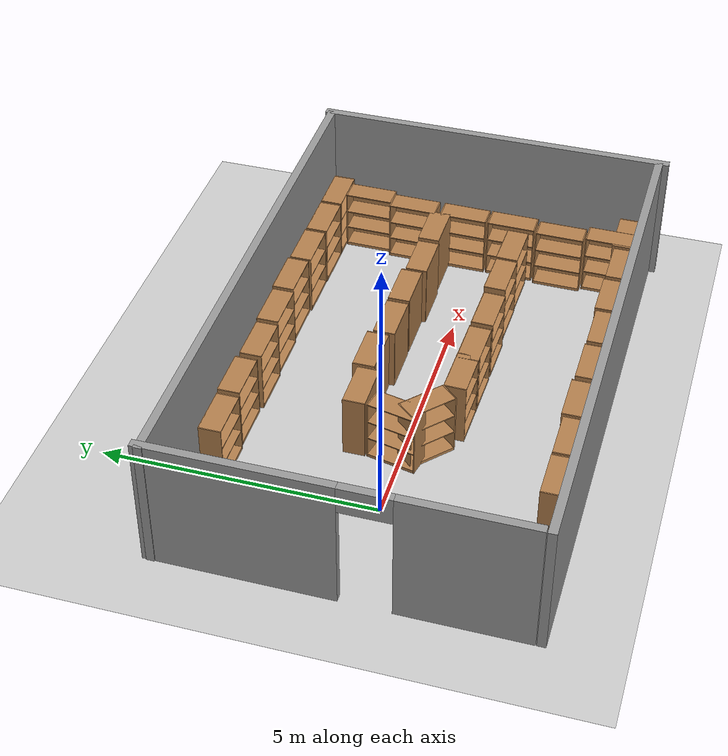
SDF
<sdf version="1.6">
 <world name="default">
  <light name="sun" type="directional">
   <pose>0 0 10 0 -0 0</pose>
   <diffuse>0.8 0.8 0.8 1</diffuse>
   <specular>0.1 0.1 0.1 1</specular>
   <attenuation>
    <range>1000</range>
    <constant>0.9</constant>
    <linear>0.01</linear>
    <quadratic>0.001</quadratic>
   </attenuation>
   <direction>-0.5 0.5 -1</direction>
  </light>
  <model name="ground_plane">
   <static>1</static>
   <link name="link">
    <collision name="collision">
     <geometry><plane><normal>0 0 1</normal><size>100 100</size></plane></geometry>
     <surface><friction><ode><mu>100</mu><mu2>50</mu2></ode></friction></surface>
    </collision>
    <visual name="visual">
     <cast_shadows>0</cast_shadows>
     <geometry><plane><normal>0 0 1</normal><size>100 100</size></plane></geometry>
     <material>
      <script><uri>file://media/materials/scripts/gazebo.material</uri><name>Gazebo/Grey</name></script>
     </material>
    </visual>
   </link>
  </model>
  <gravity>0 0 -9.8</gravity>
  <magnetic_field>6e-06 2.3e-05 -4.2e-05</magnetic_field>
  <atmosphere type="adiabatic"/>
  <physics name="default_physics" default="0" type="ode">
   <max_step_size>0.001</max_step_size>
   <real_time_factor>1</real_time_factor>
   <real_time_update_rate>1000</real_time_update_rate>
  </physics>
  <scene><ambient>0.4 0.4 0.4 1</ambient><background>0.7 0.7 0.7 1</background><shadows>1</shadows></scene>
  <spherical_coordinates>
   <surface_model>EARTH_WGS84</surface_model>
   <latitude_deg>0</latitude_deg>
   <longitude_deg>0</longitude_deg>
   <elevation>0</elevation>
   <heading_deg>0</heading_deg>
  </spherical_coordinates>
  <model name="lab">
   <pose>2.92212 0.020842 0 0 -0 0</pose>
   <link name="Wall_27">
    <collision name="Wall_27_Collision">
     <geometry><box><size>10 0.15 2.5</size></box></geometry>
     <pose>0 0 1.25 0 -0 0</pose>
    </collision>
    <visual name="Wall_27_Visual">
     <pose>0 0 1.25 0 -0 0</pose>
     <geometry><box><size>10 0.15 2.5</size></box></geometry>
     <material>
      <script><uri>file://media/materials/scripts/gazebo.material</uri><name>Gazebo/Grey</name></script>
      <ambient>1 1 1 1</ambient>
     </material>
    </visual>
    <pose>-0.035542 3.23858 0 0 -0 0</pose>
   </link>
   <link name="Wall_31">
    <collision name="Wall_31_Collision">
     <geometry><box><size>6.75 0.15 2.5</size></box></geometry>
     <pose>0 0 1.25 0 -0 0</pose>
    </collision>
    <visual name="Wall_31_Visual">
     <pose>0 0 1.25 0 -0 0</pose>
     <geometry><box><size>6.75 0.15 2.5</size></box></geometry>
     <material>
      <script><uri>file://media/materials/scripts/gazebo.material</uri><name>Gazebo/Grey</name></script>
      <ambient>1 1 1 1</ambient>
     </material>
    </visual>
    <pose>4.96054 -0.014164 0 0 0 -1.5708</pose>
   </link>
   <link name="Wall_34">
    <collision name="Wall_34_Collision">
     <geometry><box><size>10 0.15 2.5</size></box></geometry>
     <pose>0 0 1.25 0 -0 0</pose>
    </collision>
    <visual name="Wall_34_Visual">
     <pose>0 0 1.25 0 -0 0</pose>
     <geometry><box><size>10 0.15 2.5</size></box></geometry>
     <material>
      <script><uri>file://media/materials/scripts/gazebo.material</uri><name>Gazebo/Grey</name></script>
      <ambient>1 1 1 1</ambient>
     </material>
    </visual>
    <pose>-0.020866 -3.20031 0 0 -0 3.14159</pose>
   </link>
   <link name="Wall_37">
    <pose>-4.94545 0.139164 0 0 0 -1.5708</pose>
    <visual name="Wall_37_Visual_0">
     <pose>-1.59673 0 1.25 0 -0 0</pose>
     <geometry><box><size>3.30655 0.15 2.5</size></box></geometry>
     <material>
      <script><uri>file://media/materials/scripts/gazebo.material</uri><name>Gazebo/Grey</name></script>
      <ambient>1 1 1 1</ambient>
     </material>
    </visual>
    <collision name="Wall_37_Collision_0">
     <geometry><box><size>3.30655 0.15 2.5</size></box></geometry>
     <pose>-1.59673 0 1.25 0 -0 0</pose>
    </collision>
    <visual name="Wall_37_Visual_1">
     <pose>2.10327 0 1.25 0 -0 0</pose>
     <geometry><box><size>2.29345 0.15 2.5</size></box></geometry>
     <material>
      <script><uri>file://media/materials/scripts/gazebo.material</uri><name>Gazebo/Grey</name></script>
      <ambient>1 1 1 1</ambient>
     </material>
    </visual>
    <collision name="Wall_37_Collision_1">
     <geometry><box><size>2.29345 0.15 2.5</size></box></geometry>
     <pose>2.10327 0 1.25 0 -0 0</pose>
    </collision>
    <visual name="Wall_37_Visual_2">
     <pose>0.506549 0 2.25 0 -0 0</pose>
     <geometry><box><size>0.9 0.15 0.5</size></box></geometry>
     <material>
      <script><uri>file://media/materials/scripts/gazebo.material</uri><name>Gazebo/Grey</name></script>
      <ambient>1 1 1 1</ambient>
     </material>
    </visual>
    <collision name="Wall_37_Collision_2">
     <geometry><box><size>0.9 0.15 0.5</size></box></geometry>
     <pose>0.506549 0 2.25 0 -0 0</pose>
    </collision>
   </link>
   <static>1</static>
  </model>
  <model name="bookshelf_0">
   <static>1</static>
   <link name="link">
    <inertial><mass>1</mass></inertial>
    <collision name="back">
     <pose>0 0.005 0.6 0 -0 0</pose>
     <geometry><box><size>0.9 0.01 1.2</size></box></geometry>
    </collision>
    <visual name="visual1">
     <pose>0 0.005 0.6 0 -0 0</pose>
     <geometry><box><size>0.9 0.01 1.2</size></box></geometry>
     <material>
      <script><uri>file://media/materials/scripts/gazebo.material</uri><name>Gazebo/Wood</name></script>
     </material>
    </visual>
    <collision name="left_side">
     <pose>0.45 -0.195 0.6 0 -0 0</pose>
     <geometry><box><size>0.02 0.4 1.2</size></box></geometry>
    </collision>
    <visual name="visual2">
     <pose>0.45 -0.195 0.6 0 -0 0</pose>
     <geometry><box><size>0.02 0.4 1.2</size></box></geometry>
     <material>
      <script><uri>file://media/materials/scripts/gazebo.material</uri><name>Gazebo/Wood</name></script>
     </material>
    </visual>
    <collision name="right_side">
     <pose>-0.45 -0.195 0.6 0 -0 0</pose>
     <geometry><box><size>0.02 0.4 1.2</size></box></geometry>
    </collision>
    <visual name="visual3">
     <pose>-0.45 -0.195 0.6 0 -0 0</pose>
     <geometry><box><size>0.02 0.4 1.2</size></box></geometry>
     <material>
      <script><uri>file://media/materials/scripts/gazebo.material</uri><name>Gazebo/Wood</name></script>
     </material>
    </visual>
    <collision name="bottom">
     <pose>0 -0.195 0.03 0 -0 0</pose>
     <geometry><box><size>0.88 0.4 0.06</size></box></geometry>
    </collision>
    <visual name="visual4">
     <pose>0 -0.195 0.03 0 -0 0</pose>
     <geometry><box><size>0.88 0.4 0.06</size></box></geometry>
     <material>
      <script><uri>file://media/materials/scripts/gazebo.material</uri><name>Gazebo/Wood</name></script>
     </material>
    </visual>
    <collision name="top">
     <pose>0 -0.195 1.19 0 -0 0</pose>
     <geometry><box><size>0.88 0.4 0.02</size></box></geometry>
    </collision>
    <visual name="visual5">
     <pose>0 -0.195 1.19 0 -0 0</pose>
     <geometry><box><size>0.88 0.4 0.02</size></box></geometry>
     <material>
      <script><uri>file://media/materials/scripts/gazebo.material</uri><name>Gazebo/Wood</name></script>
     </material>
    </visual>
    <collision name="low_shelf">
     <pose>0 -0.195 0.43 0 -0 0</pose>
     <geometry><box><size>0.88 0.4 0.02</size></box></geometry>
    </collision>
    <visual name="visual6">
     <pose>0 -0.195 0.43 0 -0 0</pose>
     <geometry><box><size>0.88 0.4 0.02</size></box></geometry>
     <material>
      <script><uri>file://media/materials/scripts/gazebo.material</uri><name>Gazebo/Wood</name></script>
     </material>
    </visual>
    <collision name="high_shelf">
     <pose>0 -0.195 0.8 0 -0 0</pose>
     <geometry><box><size>0.88 0.4 0.02</size></box></geometry>
    </collision>
    <visual name="visual7">
     <pose>0 -0.195 0.8 0 -0 0</pose>
     <geometry><box><size>0.88 0.4 0.02</size></box></geometry>
     <material>
      <script><uri>file://media/materials/scripts/gazebo.material</uri><name>Gazebo/Wood</name></script>
     </material>
    </visual>
   </link>
   <pose>7.12078 3.11649 0 0 -0 0</pose>
  </model>
  <model name="bookshelf_0_clone">
   <static>1</static>
   <link name="link">
    <inertial><mass>1</mass></inertial>
    <collision name="back">
     <pose>0 0.005 0.6 0 -0 0</pose>
     <geometry><box><size>0.9 0.01 1.2</size></box></geometry>
    </collision>
    <visual name="visual1">
     <pose>0 0.005 0.6 0 -0 0</pose>
     <geometry><box><size>0.9 0.01 1.2</size></box></geometry>
     <material>
      <script><uri>file://media/materials/scripts/gazebo.material</uri><name>Gazebo/Wood</name></script>
     </material>
    </visual>
    <collision name="left_side">
     <pose>0.45 -0.195 0.6 0 -0 0</pose>
     <geometry><box><size>0.02 0.4 1.2</size></box></geometry>
    </collision>
    <visual name="visual2">
     <pose>0.45 -0.195 0.6 0 -0 0</pose>
     <geometry><box><size>0.02 0.4 1.2</size></box></geometry>
     <material>
      <script><uri>file://media/materials/scripts/gazebo.material</uri><name>Gazebo/Wood</name></script>
     </material>
    </visual>
    <collision name="right_side">
     <pose>-0.45 -0.195 0.6 0 -0 0</pose>
     <geometry><box><size>0.02 0.4 1.2</size></box></geometry>
    </collision>
    <visual name="visual3">
     <pose>-0.45 -0.195 0.6 0 -0 0</pose>
     <geometry><box><size>0.02 0.4 1.2</size></box></geometry>
     <material>
      <script><uri>file://media/materials/scripts/gazebo.material</uri><name>Gazebo/Wood</name></script>
     </material>
    </visual>
    <collision name="bottom">
     <pose>0 -0.195 0.03 0 -0 0</pose>
     <geometry><box><size>0.88 0.4 0.06</size></box></geometry>
    </collision>
    <visual name="visual4">
     <pose>0 -0.195 0.03 0 -0 0</pose>
     <geometry><box><size>0.88 0.4 0.06</size></box></geometry>
     <material>
      <script><uri>file://media/materials/scripts/gazebo.material</uri><name>Gazebo/Wood</name></script>
     </material>
    </visual>
    <collision name="top">
     <pose>0 -0.195 1.19 0 -0 0</pose>
     <geometry><box><size>0.88 0.4 0.02</size></box></geometry>
    </collision>
    <visual name="visual5">
     <pose>0 -0.195 1.19 0 -0 0</pose>
     <geometry><box><size>0.88 0.4 0.02</size></box></geometry>
     <material>
      <script><uri>file://media/materials/scripts/gazebo.material</uri><name>Gazebo/Wood</name></script>
     </material>
    </visual>
    <collision name="low_shelf">
     <pose>0 -0.195 0.43 0 -0 0</pose>
     <geometry><box><size>0.88 0.4 0.02</size></box></geometry>
    </collision>
    <visual name="visual6">
     <pose>0 -0.195 0.43 0 -0 0</pose>
     <geometry><box><size>0.88 0.4 0.02</size></box></geometry>
     <material>
      <script><uri>file://media/materials/scripts/gazebo.material</uri><name>Gazebo/Wood</name></script>
     </material>
    </visual>
    <collision name="high_shelf">
     <pose>0 -0.195 0.8 0 -0 0</pose>
     <geometry><box><size>0.88 0.4 0.02</size></box></geometry>
    </collision>
    <visual name="visual7">
     <pose>0 -0.195 0.8 0 -0 0</pose>
     <geometry><box><size>0.88 0.4 0.02</size></box></geometry>
     <material>
      <script><uri>file://media/materials/scripts/gazebo.material</uri><name>Gazebo/Wood</name></script>
     </material>
    </visual>
   </link>
   <pose>6.17473 3.11664 0 0 -0 0</pose>
  </model>
  <model name="bookshelf_0_clone_0">
   <static>1</static>
   <link name="link">
    <inertial><mass>1</mass></inertial>
    <collision name="back">
     <pose>0 0.005 0.6 0 -0 0</pose>
     <geometry><box><size>0.9 0.01 1.2</size></box></geometry>
    </collision>
    <visual name="visual1">
     <pose>0 0.005 0.6 0 -0 0</pose>
     <geometry><box><size>0.9 0.01 1.2</size></box></geometry>
     <material>
      <script><uri>file://media/materials/scripts/gazebo.material</uri><name>Gazebo/Wood</name></script>
     </material>
    </visual>
    <collision name="left_side">
     <pose>0.45 -0.195 0.6 0 -0 0</pose>
     <geometry><box><size>0.02 0.4 1.2</size></box></geometry>
    </collision>
    <visual name="visual2">
     <pose>0.45 -0.195 0.6 0 -0 0</pose>
     <geometry><box><size>0.02 0.4 1.2</size></box></geometry>
     <material>
      <script><uri>file://media/materials/scripts/gazebo.material</uri><name>Gazebo/Wood</name></script>
     </material>
    </visual>
    <collision name="right_side">
     <pose>-0.45 -0.195 0.6 0 -0 0</pose>
     <geometry><box><size>0.02 0.4 1.2</size></box></geometry>
    </collision>
    <visual name="visual3">
     <pose>-0.45 -0.195 0.6 0 -0 0</pose>
     <geometry><box><size>0.02 0.4 1.2</size></box></geometry>
     <material>
      <script><uri>file://media/materials/scripts/gazebo.material</uri><name>Gazebo/Wood</name></script>
     </material>
    </visual>
    <collision name="bottom">
     <pose>0 -0.195 0.03 0 -0 0</pose>
     <geometry><box><size>0.88 0.4 0.06</size></box></geometry>
    </collision>
    <visual name="visual4">
     <pose>0 -0.195 0.03 0 -0 0</pose>
     <geometry><box><size>0.88 0.4 0.06</size></box></geometry>
     <material>
      <script><uri>file://media/materials/scripts/gazebo.material</uri><name>Gazebo/Wood</name></script>
     </material>
    </visual>
    <collision name="top">
     <pose>0 -0.195 1.19 0 -0 0</pose>
     <geometry><box><size>0.88 0.4 0.02</size></box></geometry>
    </collision>
    <visual name="visual5">
     <pose>0 -0.195 1.19 0 -0 0</pose>
     <geometry><box><size>0.88 0.4 0.02</size></box></geometry>
     <material>
      <script><uri>file://media/materials/scripts/gazebo.material</uri><name>Gazebo/Wood</name></script>
     </material>
    </visual>
    <collision name="low_shelf">
     <pose>0 -0.195 0.43 0 -0 0</pose>
     <geometry><box><size>0.88 0.4 0.02</size></box></geometry>
    </collision>
    <visual name="visual6">
     <pose>0 -0.195 0.43 0 -0 0</pose>
     <geometry><box><size>0.88 0.4 0.02</size></box></geometry>
     <material>
      <script><uri>file://media/materials/scripts/gazebo.material</uri><name>Gazebo/Wood</name></script>
     </material>
    </visual>
    <collision name="high_shelf">
     <pose>0 -0.195 0.8 0 -0 0</pose>
     <geometry><box><size>0.88 0.4 0.02</size></box></geometry>
    </collision>
    <visual name="visual7">
     <pose>0 -0.195 0.8 0 -0 0</pose>
     <geometry><box><size>0.88 0.4 0.02</size></box></geometry>
     <material>
      <script><uri>file://media/materials/scripts/gazebo.material</uri><name>Gazebo/Wood</name></script>
     </material>
    </visual>
   </link>
   <pose>5.22479 3.12787 0 0 -0 0</pose>
  </model>
  <model name="bookshelf_0_clone_1">
   <static>1</static>
   <link name="link">
    <inertial><mass>1</mass></inertial>
    <collision name="back">
     <pose>0 0.005 0.6 0 -0 0</pose>
     <geometry><box><size>0.9 0.01 1.2</size></box></geometry>
    </collision>
    <visual name="visual1">
     <pose>0 0.005 0.6 0 -0 0</pose>
     <geometry><box><size>0.9 0.01 1.2</size></box></geometry>
     <material>
      <script><uri>file://media/materials/scripts/gazebo.material</uri><name>Gazebo/Wood</name></script>
     </material>
    </visual>
    <collision name="left_side">
     <pose>0.45 -0.195 0.6 0 -0 0</pose>
     <geometry><box><size>0.02 0.4 1.2</size></box></geometry>
    </collision>
    <visual name="visual2">
     <pose>0.45 -0.195 0.6 0 -0 0</pose>
     <geometry><box><size>0.02 0.4 1.2</size></box></geometry>
     <material>
      <script><uri>file://media/materials/scripts/gazebo.material</uri><name>Gazebo/Wood</name></script>
     </material>
    </visual>
    <collision name="right_side">
     <pose>-0.45 -0.195 0.6 0 -0 0</pose>
     <geometry><box><size>0.02 0.4 1.2</size></box></geometry>
    </collision>
    <visual name="visual3">
     <pose>-0.45 -0.195 0.6 0 -0 0</pose>
     <geometry><box><size>0.02 0.4 1.2</size></box></geometry>
     <material>
      <script><uri>file://media/materials/scripts/gazebo.material</uri><name>Gazebo/Wood</name></script>
     </material>
    </visual>
    <collision name="bottom">
     <pose>0 -0.195 0.03 0 -0 0</pose>
     <geometry><box><size>0.88 0.4 0.06</size></box></geometry>
    </collision>
    <visual name="visual4">
     <pose>0 -0.195 0.03 0 -0 0</pose>
     <geometry><box><size>0.88 0.4 0.06</size></box></geometry>
     <material>
      <script><uri>file://media/materials/scripts/gazebo.material</uri><name>Gazebo/Wood</name></script>
     </material>
    </visual>
    <collision name="top">
     <pose>0 -0.195 1.19 0 -0 0</pose>
     <geometry><box><size>0.88 0.4 0.02</size></box></geometry>
    </collision>
    <visual name="visual5">
     <pose>0 -0.195 1.19 0 -0 0</pose>
     <geometry><box><size>0.88 0.4 0.02</size></box></geometry>
     <material>
      <script><uri>file://media/materials/scripts/gazebo.material</uri><name>Gazebo/Wood</name></script>
     </material>
    </visual>
    <collision name="low_shelf">
     <pose>0 -0.195 0.43 0 -0 0</pose>
     <geometry><box><size>0.88 0.4 0.02</size></box></geometry>
    </collision>
    <visual name="visual6">
     <pose>0 -0.195 0.43 0 -0 0</pose>
     <geometry><box><size>0.88 0.4 0.02</size></box></geometry>
     <material>
      <script><uri>file://media/materials/scripts/gazebo.material</uri><name>Gazebo/Wood</name></script>
     </material>
    </visual>
    <collision name="high_shelf">
     <pose>0 -0.195 0.8 0 -0 0</pose>
     <geometry><box><size>0.88 0.4 0.02</size></box></geometry>
    </collision>
    <visual name="visual7">
     <pose>0 -0.195 0.8 0 -0 0</pose>
     <geometry><box><size>0.88 0.4 0.02</size></box></geometry>
     <material>
      <script><uri>file://media/materials/scripts/gazebo.material</uri><name>Gazebo/Wood</name></script>
     </material>
    </visual>
   </link>
   <pose>4.28509 3.15898 0 0 -0 0</pose>
  </model>
  <model name="bookshelf_0_clone_2">
   <static>1</static>
   <link name="link">
    <inertial><mass>1</mass></inertial>
    <collision name="back">
     <pose>0 0.005 0.6 0 -0 0</pose>
     <geometry><box><size>0.9 0.01 1.2</size></box></geometry>
    </collision>
    <visual name="visual1">
     <pose>0 0.005 0.6 0 -0 0</pose>
     <geometry><box><size>0.9 0.01 1.2</size></box></geometry>
     <material>
      <script><uri>file://media/materials/scripts/gazebo.material</uri><name>Gazebo/Wood</name></script>
     </material>
    </visual>
    <collision name="left_side">
     <pose>0.45 -0.195 0.6 0 -0 0</pose>
     <geometry><box><size>0.02 0.4 1.2</size></box></geometry>
    </collision>
    <visual name="visual2">
     <pose>0.45 -0.195 0.6 0 -0 0</pose>
     <geometry><box><size>0.02 0.4 1.2</size></box></geometry>
     <material>
      <script><uri>file://media/materials/scripts/gazebo.material</uri><name>Gazebo/Wood</name></script>
     </material>
    </visual>
    <collision name="right_side">
     <pose>-0.45 -0.195 0.6 0 -0 0</pose>
     <geometry><box><size>0.02 0.4 1.2</size></box></geometry>
    </collision>
    <visual name="visual3">
     <pose>-0.45 -0.195 0.6 0 -0 0</pose>
     <geometry><box><size>0.02 0.4 1.2</size></box></geometry>
     <material>
      <script><uri>file://media/materials/scripts/gazebo.material</uri><name>Gazebo/Wood</name></script>
     </material>
    </visual>
    <collision name="bottom">
     <pose>0 -0.195 0.03 0 -0 0</pose>
     <geometry><box><size>0.88 0.4 0.06</size></box></geometry>
    </collision>
    <visual name="visual4">
     <pose>0 -0.195 0.03 0 -0 0</pose>
     <geometry><box><size>0.88 0.4 0.06</size></box></geometry>
     <material>
      <script><uri>file://media/materials/scripts/gazebo.material</uri><name>Gazebo/Wood</name></script>
     </material>
    </visual>
    <collision name="top">
     <pose>0 -0.195 1.19 0 -0 0</pose>
     <geometry><box><size>0.88 0.4 0.02</size></box></geometry>
    </collision>
    <visual name="visual5">
     <pose>0 -0.195 1.19 0 -0 0</pose>
     <geometry><box><size>0.88 0.4 0.02</size></box></geometry>
     <material>
      <script><uri>file://media/materials/scripts/gazebo.material</uri><name>Gazebo/Wood</name></script>
     </material>
    </visual>
    <collision name="low_shelf">
     <pose>0 -0.195 0.43 0 -0 0</pose>
     <geometry><box><size>0.88 0.4 0.02</size></box></geometry>
    </collision>
    <visual name="visual6">
     <pose>0 -0.195 0.43 0 -0 0</pose>
     <geometry><box><size>0.88 0.4 0.02</size></box></geometry>
     <material>
      <script><uri>file://media/materials/scripts/gazebo.material</uri><name>Gazebo/Wood</name></script>
     </material>
    </visual>
    <collision name="high_shelf">
     <pose>0 -0.195 0.8 0 -0 0</pose>
     <geometry><box><size>0.88 0.4 0.02</size></box></geometry>
    </collision>
    <visual name="visual7">
     <pose>0 -0.195 0.8 0 -0 0</pose>
     <geometry><box><size>0.88 0.4 0.02</size></box></geometry>
     <material>
      <script><uri>file://media/materials/scripts/gazebo.material</uri><name>Gazebo/Wood</name></script>
     </material>
    </visual>
   </link>
   <pose>3.31626 3.12697 0 0 -0 0</pose>
  </model>
  <model name="bookshelf_0_clone_3">
   <static>1</static>
   <link name="link">
    <inertial><mass>1</mass></inertial>
    <collision name="back">
     <pose>0 0.005 0.6 0 -0 0</pose>
     <geometry><box><size>0.9 0.01 1.2</size></box></geometry>
    </collision>
    <visual name="visual1">
     <pose>0 0.005 0.6 0 -0 0</pose>
     <geometry><box><size>0.9 0.01 1.2</size></box></geometry>
     <material>
      <script><uri>file://media/materials/scripts/gazebo.material</uri><name>Gazebo/Wood</name></script>
     </material>
    </visual>
    <collision name="left_side">
     <pose>0.45 -0.195 0.6 0 -0 0</pose>
     <geometry><box><size>0.02 0.4 1.2</size></box></geometry>
    </collision>
    <visual name="visual2">
     <pose>0.45 -0.195 0.6 0 -0 0</pose>
     <geometry><box><size>0.02 0.4 1.2</size></box></geometry>
     <material>
      <script><uri>file://media/materials/scripts/gazebo.material</uri><name>Gazebo/Wood</name></script>
     </material>
    </visual>
    <collision name="right_side">
     <pose>-0.45 -0.195 0.6 0 -0 0</pose>
     <geometry><box><size>0.02 0.4 1.2</size></box></geometry>
    </collision>
    <visual name="visual3">
     <pose>-0.45 -0.195 0.6 0 -0 0</pose>
     <geometry><box><size>0.02 0.4 1.2</size></box></geometry>
     <material>
      <script><uri>file://media/materials/scripts/gazebo.material</uri><name>Gazebo/Wood</name></script>
     </material>
    </visual>
    <collision name="bottom">
     <pose>0 -0.195 0.03 0 -0 0</pose>
     <geometry><box><size>0.88 0.4 0.06</size></box></geometry>
    </collision>
    <visual name="visual4">
     <pose>0 -0.195 0.03 0 -0 0</pose>
     <geometry><box><size>0.88 0.4 0.06</size></box></geometry>
     <material>
      <script><uri>file://media/materials/scripts/gazebo.material</uri><name>Gazebo/Wood</name></script>
     </material>
    </visual>
    <collision name="top">
     <pose>0 -0.195 1.19 0 -0 0</pose>
     <geometry><box><size>0.88 0.4 0.02</size></box></geometry>
    </collision>
    <visual name="visual5">
     <pose>0 -0.195 1.19 0 -0 0</pose>
     <geometry><box><size>0.88 0.4 0.02</size></box></geometry>
     <material>
      <script><uri>file://media/materials/scripts/gazebo.material</uri><name>Gazebo/Wood</name></script>
     </material>
    </visual>
    <collision name="low_shelf">
     <pose>0 -0.195 0.43 0 -0 0</pose>
     <geometry><box><size>0.88 0.4 0.02</size></box></geometry>
    </collision>
    <visual name="visual6">
     <pose>0 -0.195 0.43 0 -0 0</pose>
     <geometry><box><size>0.88 0.4 0.02</size></box></geometry>
     <material>
      <script><uri>file://media/materials/scripts/gazebo.material</uri><name>Gazebo/Wood</name></script>
     </material>
    </visual>
    <collision name="high_shelf">
     <pose>0 -0.195 0.8 0 -0 0</pose>
     <geometry><box><size>0.88 0.4 0.02</size></box></geometry>
    </collision>
    <visual name="visual7">
     <pose>0 -0.195 0.8 0 -0 0</pose>
     <geometry><box><size>0.88 0.4 0.02</size></box></geometry>
     <material>
      <script><uri>file://media/materials/scripts/gazebo.material</uri><name>Gazebo/Wood</name></script>
     </material>
    </visual>
   </link>
   <pose>2.33101 3.09869 0 0 -0 0</pose>
  </model>
  <model name="bookshelf_0_clone_4">
   <static>1</static>
   <link name="link">
    <inertial><mass>1</mass></inertial>
    <collision name="back">
     <pose>0 0.005 0.6 0 -0 0</pose>
     <geometry><box><size>0.9 0.01 1.2</size></box></geometry>
    </collision>
    <visual name="visual1">
     <pose>0 0.005 0.6 0 -0 0</pose>
     <geometry><box><size>0.9 0.01 1.2</size></box></geometry>
     <material>
      <script><uri>file://media/materials/scripts/gazebo.material</uri><name>Gazebo/Wood</name></script>
     </material>
    </visual>
    <collision name="left_side">
     <pose>0.45 -0.195 0.6 0 -0 0</pose>
     <geometry><box><size>0.02 0.4 1.2</size></box></geometry>
    </collision>
    <visual name="visual2">
     <pose>0.45 -0.195 0.6 0 -0 0</pose>
     <geometry><box><size>0.02 0.4 1.2</size></box></geometry>
     <material>
      <script><uri>file://media/materials/scripts/gazebo.material</uri><name>Gazebo/Wood</name></script>
     </material>
    </visual>
    <collision name="right_side">
     <pose>-0.45 -0.195 0.6 0 -0 0</pose>
     <geometry><box><size>0.02 0.4 1.2</size></box></geometry>
    </collision>
    <visual name="visual3">
     <pose>-0.45 -0.195 0.6 0 -0 0</pose>
     <geometry><box><size>0.02 0.4 1.2</size></box></geometry>
     <material>
      <script><uri>file://media/materials/scripts/gazebo.material</uri><name>Gazebo/Wood</name></script>
     </material>
    </visual>
    <collision name="bottom">
     <pose>0 -0.195 0.03 0 -0 0</pose>
     <geometry><box><size>0.88 0.4 0.06</size></box></geometry>
    </collision>
    <visual name="visual4">
     <pose>0 -0.195 0.03 0 -0 0</pose>
     <geometry><box><size>0.88 0.4 0.06</size></box></geometry>
     <material>
      <script><uri>file://media/materials/scripts/gazebo.material</uri><name>Gazebo/Wood</name></script>
     </material>
    </visual>
    <collision name="top">
     <pose>0 -0.195 1.19 0 -0 0</pose>
     <geometry><box><size>0.88 0.4 0.02</size></box></geometry>
    </collision>
    <visual name="visual5">
     <pose>0 -0.195 1.19 0 -0 0</pose>
     <geometry><box><size>0.88 0.4 0.02</size></box></geometry>
     <material>
      <script><uri>file://media/materials/scripts/gazebo.material</uri><name>Gazebo/Wood</name></script>
     </material>
    </visual>
    <collision name="low_shelf">
     <pose>0 -0.195 0.43 0 -0 0</pose>
     <geometry><box><size>0.88 0.4 0.02</size></box></geometry>
    </collision>
    <visual name="visual6">
     <pose>0 -0.195 0.43 0 -0 0</pose>
     <geometry><box><size>0.88 0.4 0.02</size></box></geometry>
     <material>
      <script><uri>file://media/materials/scripts/gazebo.material</uri><name>Gazebo/Wood</name></script>
     </material>
    </visual>
    <collision name="high_shelf">
     <pose>0 -0.195 0.8 0 -0 0</pose>
     <geometry><box><size>0.88 0.4 0.02</size></box></geometry>
    </collision>
    <visual name="visual7">
     <pose>0 -0.195 0.8 0 -0 0</pose>
     <geometry><box><size>0.88 0.4 0.02</size></box></geometry>
     <material>
      <script><uri>file://media/materials/scripts/gazebo.material</uri><name>Gazebo/Wood</name></script>
     </material>
    </visual>
   </link>
   <pose>1.31983 3.13726 0 0 -0 0</pose>
  </model>
  <model name="bookshelf_0_clone_5">
   <static>1</static>
   <link name="link">
    <inertial><mass>1</mass></inertial>
    <collision name="back">
     <pose>0 0.005 0.6 0 -0 0</pose>
     <geometry><box><size>0.9 0.01 1.2</size></box></geometry>
    </collision>
    <visual name="visual1">
     <pose>0 0.005 0.6 0 -0 0</pose>
     <geometry><box><size>0.9 0.01 1.2</size></box></geometry>
     <material>
      <script><uri>file://media/materials/scripts/gazebo.material</uri><name>Gazebo/Wood</name></script>
     </material>
    </visual>
    <collision name="left_side">
     <pose>0.45 -0.195 0.6 0 -0 0</pose>
     <geometry><box><size>0.02 0.4 1.2</size></box></geometry>
    </collision>
    <visual name="visual2">
     <pose>0.45 -0.195 0.6 0 -0 0</pose>
     <geometry><box><size>0.02 0.4 1.2</size></box></geometry>
     <material>
      <script><uri>file://media/materials/scripts/gazebo.material</uri><name>Gazebo/Wood</name></script>
     </material>
    </visual>
    <collision name="right_side">
     <pose>-0.45 -0.195 0.6 0 -0 0</pose>
     <geometry><box><size>0.02 0.4 1.2</size></box></geometry>
    </collision>
    <visual name="visual3">
     <pose>-0.45 -0.195 0.6 0 -0 0</pose>
     <geometry><box><size>0.02 0.4 1.2</size></box></geometry>
     <material>
      <script><uri>file://media/materials/scripts/gazebo.material</uri><name>Gazebo/Wood</name></script>
     </material>
    </visual>
    <collision name="bottom">
     <pose>0 -0.195 0.03 0 -0 0</pose>
     <geometry><box><size>0.88 0.4 0.06</size></box></geometry>
    </collision>
    <visual name="visual4">
     <pose>0 -0.195 0.03 0 -0 0</pose>
     <geometry><box><size>0.88 0.4 0.06</size></box></geometry>
     <material>
      <script><uri>file://media/materials/scripts/gazebo.material</uri><name>Gazebo/Wood</name></script>
     </material>
    </visual>
    <collision name="top">
     <pose>0 -0.195 1.19 0 -0 0</pose>
     <geometry><box><size>0.88 0.4 0.02</size></box></geometry>
    </collision>
    <visual name="visual5">
     <pose>0 -0.195 1.19 0 -0 0</pose>
     <geometry><box><size>0.88 0.4 0.02</size></box></geometry>
     <material>
      <script><uri>file://media/materials/scripts/gazebo.material</uri><name>Gazebo/Wood</name></script>
     </material>
    </visual>
    <collision name="low_shelf">
     <pose>0 -0.195 0.43 0 -0 0</pose>
     <geometry><box><size>0.88 0.4 0.02</size></box></geometry>
    </collision>
    <visual name="visual6">
     <pose>0 -0.195 0.43 0 -0 0</pose>
     <geometry><box><size>0.88 0.4 0.02</size></box></geometry>
     <material>
      <script><uri>file://media/materials/scripts/gazebo.material</uri><name>Gazebo/Wood</name></script>
     </material>
    </visual>
    <collision name="high_shelf">
     <pose>0 -0.195 0.8 0 -0 0</pose>
     <geometry><box><size>0.88 0.4 0.02</size></box></geometry>
    </collision>
    <visual name="visual7">
     <pose>0 -0.195 0.8 0 -0 0</pose>
     <geometry><box><size>0.88 0.4 0.02</size></box></geometry>
     <material>
      <script><uri>file://media/materials/scripts/gazebo.material</uri><name>Gazebo/Wood</name></script>
     </material>
    </visual>
   </link>
   <pose>0.321179 3.10913 0 0 -0 0</pose>
  </model>
  <model name="bookshelf_0_clone_6_clone">
   <static>1</static>
   <link name="link">
    <inertial><mass>1</mass></inertial>
    <collision name="back">
     <pose>0 0.005 0.6 0 -0 0</pose>
     <geometry><box><size>0.9 0.01 1.2</size></box></geometry>
    </collision>
    <visual name="visual1">
     <pose>0 0.005 0.6 0 -0 0</pose>
     <geometry><box><size>0.9 0.01 1.2</size></box></geometry>
     <material>
      <script><uri>file://media/materials/scripts/gazebo.material</uri><name>Gazebo/Wood</name></script>
     </material>
    </visual>
    <collision name="left_side">
     <pose>0.45 -0.195 0.6 0 -0 0</pose>
     <geometry><box><size>0.02 0.4 1.2</size></box></geometry>
    </collision>
    <visual name="visual2">
     <pose>0.45 -0.195 0.6 0 -0 0</pose>
     <geometry><box><size>0.02 0.4 1.2</size></box></geometry>
     <material>
      <script><uri>file://media/materials/scripts/gazebo.material</uri><name>Gazebo/Wood</name></script>
     </material>
    </visual>
    <collision name="right_side">
     <pose>-0.45 -0.195 0.6 0 -0 0</pose>
     <geometry><box><size>0.02 0.4 1.2</size></box></geometry>
    </collision>
    <visual name="visual3">
     <pose>-0.45 -0.195 0.6 0 -0 0</pose>
     <geometry><box><size>0.02 0.4 1.2</size></box></geometry>
     <material>
      <script><uri>file://media/materials/scripts/gazebo.material</uri><name>Gazebo/Wood</name></script>
     </material>
    </visual>
    <collision name="bottom">
     <pose>0 -0.195 0.03 0 -0 0</pose>
     <geometry><box><size>0.88 0.4 0.06</size></box></geometry>
    </collision>
    <visual name="visual4">
     <pose>0 -0.195 0.03 0 -0 0</pose>
     <geometry><box><size>0.88 0.4 0.06</size></box></geometry>
     <material>
      <script><uri>file://media/materials/scripts/gazebo.material</uri><name>Gazebo/Wood</name></script>
     </material>
    </visual>
    <collision name="top">
     <pose>0 -0.195 1.19 0 -0 0</pose>
     <geometry><box><size>0.88 0.4 0.02</size></box></geometry>
    </collision>
    <visual name="visual5">
     <pose>0 -0.195 1.19 0 -0 0</pose>
     <geometry><box><size>0.88 0.4 0.02</size></box></geometry>
     <material>
      <script><uri>file://media/materials/scripts/gazebo.material</uri><name>Gazebo/Wood</name></script>
     </material>
    </visual>
    <collision name="low_shelf">
     <pose>0 -0.195 0.43 0 -0 0</pose>
     <geometry><box><size>0.88 0.4 0.02</size></box></geometry>
    </collision>
    <visual name="visual6">
     <pose>0 -0.195 0.43 0 -0 0</pose>
     <geometry><box><size>0.88 0.4 0.02</size></box></geometry>
     <material>
      <script><uri>file://media/materials/scripts/gazebo.material</uri><name>Gazebo/Wood</name></script>
     </material>
    </visual>
    <collision name="high_shelf">
     <pose>0 -0.195 0.8 0 -0 0</pose>
     <geometry><box><size>0.88 0.4 0.02</size></box></geometry>
    </collision>
    <visual name="visual7">
     <pose>0 -0.195 0.8 0 -0 0</pose>
     <geometry><box><size>0.88 0.4 0.02</size></box></geometry>
     <material>
      <script><uri>file://media/materials/scripts/gazebo.material</uri><name>Gazebo/Wood</name></script>
     </material>
    </visual>
   </link>
   <pose>6.29282 -3.03785 0 0 -0 3.14</pose>
  </model>
  <model name="bookshelf_0_clone_6_clone_clone">
   <static>1</static>
   <link name="link">
    <inertial><mass>1</mass></inertial>
    <collision name="back">
     <pose>0 0.005 0.6 0 -0 0</pose>
     <geometry><box><size>0.9 0.01 1.2</size></box></geometry>
    </collision>
    <visual name="visual1">
     <pose>0 0.005 0.6 0 -0 0</pose>
     <geometry><box><size>0.9 0.01 1.2</size></box></geometry>
     <material>
      <script><uri>file://media/materials/scripts/gazebo.material</uri><name>Gazebo/Wood</name></script>
     </material>
    </visual>
    <collision name="left_side">
     <pose>0.45 -0.195 0.6 0 -0 0</pose>
     <geometry><box><size>0.02 0.4 1.2</size></box></geometry>
    </collision>
    <visual name="visual2">
     <pose>0.45 -0.195 0.6 0 -0 0</pose>
     <geometry><box><size>0.02 0.4 1.2</size></box></geometry>
     <material>
      <script><uri>file://media/materials/scripts/gazebo.material</uri><name>Gazebo/Wood</name></script>
     </material>
    </visual>
    <collision name="right_side">
     <pose>-0.45 -0.195 0.6 0 -0 0</pose>
     <geometry><box><size>0.02 0.4 1.2</size></box></geometry>
    </collision>
    <visual name="visual3">
     <pose>-0.45 -0.195 0.6 0 -0 0</pose>
     <geometry><box><size>0.02 0.4 1.2</size></box></geometry>
     <material>
      <script><uri>file://media/materials/scripts/gazebo.material</uri><name>Gazebo/Wood</name></script>
     </material>
    </visual>
    <collision name="bottom">
     <pose>0 -0.195 0.03 0 -0 0</pose>
     <geometry><box><size>0.88 0.4 0.06</size></box></geometry>
    </collision>
    <visual name="visual4">
     <pose>0 -0.195 0.03 0 -0 0</pose>
     <geometry><box><size>0.88 0.4 0.06</size></box></geometry>
     <material>
      <script><uri>file://media/materials/scripts/gazebo.material</uri><name>Gazebo/Wood</name></script>
     </material>
    </visual>
    <collision name="top">
     <pose>0 -0.195 1.19 0 -0 0</pose>
     <geometry><box><size>0.88 0.4 0.02</size></box></geometry>
    </collision>
    <visual name="visual5">
     <pose>0 -0.195 1.19 0 -0 0</pose>
     <geometry><box><size>0.88 0.4 0.02</size></box></geometry>
     <material>
      <script><uri>file://media/materials/scripts/gazebo.material</uri><name>Gazebo/Wood</name></script>
     </material>
    </visual>
    <collision name="low_shelf">
     <pose>0 -0.195 0.43 0 -0 0</pose>
     <geometry><box><size>0.88 0.4 0.02</size></box></geometry>
    </collision>
    <visual name="visual6">
     <pose>0 -0.195 0.43 0 -0 0</pose>
     <geometry><box><size>0.88 0.4 0.02</size></box></geometry>
     <material>
      <script><uri>file://media/materials/scripts/gazebo.material</uri><name>Gazebo/Wood</name></script>
     </material>
    </visual>
    <collision name="high_shelf">
     <pose>0 -0.195 0.8 0 -0 0</pose>
     <geometry><box><size>0.88 0.4 0.02</size></box></geometry>
    </collision>
    <visual name="visual7">
     <pose>0 -0.195 0.8 0 -0 0</pose>
     <geometry><box><size>0.88 0.4 0.02</size></box></geometry>
     <material>
      <script><uri>file://media/materials/scripts/gazebo.material</uri><name>Gazebo/Wood</name></script>
     </material>
    </visual>
   </link>
   <pose>7.26558 -2.99057 0 0 -0 3.14</pose>
  </model>
  <model name="bookshelf_0_clone_6_clone_clone_0">
   <static>1</static>
   <link name="link">
    <inertial><mass>1</mass></inertial>
    <collision name="back">
     <pose>0 0.005 0.6 0 -0 0</pose>
     <geometry><box><size>0.9 0.01 1.2</size></box></geometry>
    </collision>
    <visual name="visual1">
     <pose>0 0.005 0.6 0 -0 0</pose>
     <geometry><box><size>0.9 0.01 1.2</size></box></geometry>
     <material>
      <script><uri>file://media/materials/scripts/gazebo.material</uri><name>Gazebo/Wood</name></script>
     </material>
    </visual>
    <collision name="left_side">
     <pose>0.45 -0.195 0.6 0 -0 0</pose>
     <geometry><box><size>0.02 0.4 1.2</size></box></geometry>
    </collision>
    <visual name="visual2">
     <pose>0.45 -0.195 0.6 0 -0 0</pose>
     <geometry><box><size>0.02 0.4 1.2</size></box></geometry>
     <material>
      <script><uri>file://media/materials/scripts/gazebo.material</uri><name>Gazebo/Wood</name></script>
     </material>
    </visual>
    <collision name="right_side">
     <pose>-0.45 -0.195 0.6 0 -0 0</pose>
     <geometry><box><size>0.02 0.4 1.2</size></box></geometry>
    </collision>
    <visual name="visual3">
     <pose>-0.45 -0.195 0.6 0 -0 0</pose>
     <geometry><box><size>0.02 0.4 1.2</size></box></geometry>
     <material>
      <script><uri>file://media/materials/scripts/gazebo.material</uri><name>Gazebo/Wood</name></script>
     </material>
    </visual>
    <collision name="bottom">
     <pose>0 -0.195 0.03 0 -0 0</pose>
     <geometry><box><size>0.88 0.4 0.06</size></box></geometry>
    </collision>
    <visual name="visual4">
     <pose>0 -0.195 0.03 0 -0 0</pose>
     <geometry><box><size>0.88 0.4 0.06</size></box></geometry>
     <material>
      <script><uri>file://media/materials/scripts/gazebo.material</uri><name>Gazebo/Wood</name></script>
     </material>
    </visual>
    <collision name="top">
     <pose>0 -0.195 1.19 0 -0 0</pose>
     <geometry><box><size>0.88 0.4 0.02</size></box></geometry>
    </collision>
    <visual name="visual5">
     <pose>0 -0.195 1.19 0 -0 0</pose>
     <geometry><box><size>0.88 0.4 0.02</size></box></geometry>
     <material>
      <script><uri>file://media/materials/scripts/gazebo.material</uri><name>Gazebo/Wood</name></script>
     </material>
    </visual>
    <collision name="low_shelf">
     <pose>0 -0.195 0.43 0 -0 0</pose>
     <geometry><box><size>0.88 0.4 0.02</size></box></geometry>
    </collision>
    <visual name="visual6">
     <pose>0 -0.195 0.43 0 -0 0</pose>
     <geometry><box><size>0.88 0.4 0.02</size></box></geometry>
     <material>
      <script><uri>file://media/materials/scripts/gazebo.material</uri><name>Gazebo/Wood</name></script>
     </material>
    </visual>
    <collision name="high_shelf">
     <pose>0 -0.195 0.8 0 -0 0</pose>
     <geometry><box><size>0.88 0.4 0.02</size></box></geometry>
    </collision>
    <visual name="visual7">
     <pose>0 -0.195 0.8 0 -0 0</pose>
     <geometry><box><size>0.88 0.4 0.02</size></box></geometry>
     <material>
      <script><uri>file://media/materials/scripts/gazebo.material</uri><name>Gazebo/Wood</name></script>
     </material>
    </visual>
   </link>
   <pose>5.30807 -3.01833 0 0 -0 3.14</pose>
  </model>
  <model name="bookshelf_0_clone_6_clone_clone_1">
   <static>1</static>
   <link name="link">
    <inertial><mass>1</mass></inertial>
    <collision name="back">
     <pose>0 0.005 0.6 0 -0 0</pose>
     <geometry><box><size>0.9 0.01 1.2</size></box></geometry>
    </collision>
    <visual name="visual1">
     <pose>0 0.005 0.6 0 -0 0</pose>
     <geometry><box><size>0.9 0.01 1.2</size></box></geometry>
     <material>
      <script><uri>file://media/materials/scripts/gazebo.material</uri><name>Gazebo/Wood</name></script>
     </material>
    </visual>
    <collision name="left_side">
     <pose>0.45 -0.195 0.6 0 -0 0</pose>
     <geometry><box><size>0.02 0.4 1.2</size></box></geometry>
    </collision>
    <visual name="visual2">
     <pose>0.45 -0.195 0.6 0 -0 0</pose>
     <geometry><box><size>0.02 0.4 1.2</size></box></geometry>
     <material>
      <script><uri>file://media/materials/scripts/gazebo.material</uri><name>Gazebo/Wood</name></script>
     </material>
    </visual>
    <collision name="right_side">
     <pose>-0.45 -0.195 0.6 0 -0 0</pose>
     <geometry><box><size>0.02 0.4 1.2</size></box></geometry>
    </collision>
    <visual name="visual3">
     <pose>-0.45 -0.195 0.6 0 -0 0</pose>
     <geometry><box><size>0.02 0.4 1.2</size></box></geometry>
     <material>
      <script><uri>file://media/materials/scripts/gazebo.material</uri><name>Gazebo/Wood</name></script>
     </material>
    </visual>
    <collision name="bottom">
     <pose>0 -0.195 0.03 0 -0 0</pose>
     <geometry><box><size>0.88 0.4 0.06</size></box></geometry>
    </collision>
    <visual name="visual4">
     <pose>0 -0.195 0.03 0 -0 0</pose>
     <geometry><box><size>0.88 0.4 0.06</size></box></geometry>
     <material>
      <script><uri>file://media/materials/scripts/gazebo.material</uri><name>Gazebo/Wood</name></script>
     </material>
    </visual>
    <collision name="top">
     <pose>0 -0.195 1.19 0 -0 0</pose>
     <geometry><box><size>0.88 0.4 0.02</size></box></geometry>
    </collision>
    <visual name="visual5">
     <pose>0 -0.195 1.19 0 -0 0</pose>
     <geometry><box><size>0.88 0.4 0.02</size></box></geometry>
     <material>
      <script><uri>file://media/materials/scripts/gazebo.material</uri><name>Gazebo/Wood</name></script>
     </material>
    </visual>
    <collision name="low_shelf">
     <pose>0 -0.195 0.43 0 -0 0</pose>
     <geometry><box><size>0.88 0.4 0.02</size></box></geometry>
    </collision>
    <visual name="visual6">
     <pose>0 -0.195 0.43 0 -0 0</pose>
     <geometry><box><size>0.88 0.4 0.02</size></box></geometry>
     <material>
      <script><uri>file://media/materials/scripts/gazebo.material</uri><name>Gazebo/Wood</name></script>
     </material>
    </visual>
    <collision name="high_shelf">
     <pose>0 -0.195 0.8 0 -0 0</pose>
     <geometry><box><size>0.88 0.4 0.02</size></box></geometry>
    </collision>
    <visual name="visual7">
     <pose>0 -0.195 0.8 0 -0 0</pose>
     <geometry><box><size>0.88 0.4 0.02</size></box></geometry>
     <material>
      <script><uri>file://media/materials/scripts/gazebo.material</uri><name>Gazebo/Wood</name></script>
     </material>
    </visual>
   </link>
   <pose>4.34889 -3.05257 0 0 -0 3.14</pose>
  </model>
  <model name="bookshelf_0_clone_6_clone_clone_2">
   <static>1</static>
   <link name="link">
    <inertial><mass>1</mass></inertial>
    <collision name="back">
     <pose>0 0.005 0.6 0 -0 0</pose>
     <geometry><box><size>0.9 0.01 1.2</size></box></geometry>
    </collision>
    <visual name="visual1">
     <pose>0 0.005 0.6 0 -0 0</pose>
     <geometry><box><size>0.9 0.01 1.2</size></box></geometry>
     <material>
      <script><uri>file://media/materials/scripts/gazebo.material</uri><name>Gazebo/Wood</name></script>
     </material>
    </visual>
    <collision name="left_side">
     <pose>0.45 -0.195 0.6 0 -0 0</pose>
     <geometry><box><size>0.02 0.4 1.2</size></box></geometry>
    </collision>
    <visual name="visual2">
     <pose>0.45 -0.195 0.6 0 -0 0</pose>
     <geometry><box><size>0.02 0.4 1.2</size></box></geometry>
     <material>
      <script><uri>file://media/materials/scripts/gazebo.material</uri><name>Gazebo/Wood</name></script>
     </material>
    </visual>
    <collision name="right_side">
     <pose>-0.45 -0.195 0.6 0 -0 0</pose>
     <geometry><box><size>0.02 0.4 1.2</size></box></geometry>
    </collision>
    <visual name="visual3">
     <pose>-0.45 -0.195 0.6 0 -0 0</pose>
     <geometry><box><size>0.02 0.4 1.2</size></box></geometry>
     <material>
      <script><uri>file://media/materials/scripts/gazebo.material</uri><name>Gazebo/Wood</name></script>
     </material>
    </visual>
    <collision name="bottom">
     <pose>0 -0.195 0.03 0 -0 0</pose>
     <geometry><box><size>0.88 0.4 0.06</size></box></geometry>
    </collision>
    <visual name="visual4">
     <pose>0 -0.195 0.03 0 -0 0</pose>
     <geometry><box><size>0.88 0.4 0.06</size></box></geometry>
     <material>
      <script><uri>file://media/materials/scripts/gazebo.material</uri><name>Gazebo/Wood</name></script>
     </material>
    </visual>
    <collision name="top">
     <pose>0 -0.195 1.19 0 -0 0</pose>
     <geometry><box><size>0.88 0.4 0.02</size></box></geometry>
    </collision>
    <visual name="visual5">
     <pose>0 -0.195 1.19 0 -0 0</pose>
     <geometry><box><size>0.88 0.4 0.02</size></box></geometry>
     <material>
      <script><uri>file://media/materials/scripts/gazebo.material</uri><name>Gazebo/Wood</name></script>
     </material>
    </visual>
    <collision name="low_shelf">
     <pose>0 -0.195 0.43 0 -0 0</pose>
     <geometry><box><size>0.88 0.4 0.02</size></box></geometry>
    </collision>
    <visual name="visual6">
     <pose>0 -0.195 0.43 0 -0 0</pose>
     <geometry><box><size>0.88 0.4 0.02</size></box></geometry>
     <material>
      <script><uri>file://media/materials/scripts/gazebo.material</uri><name>Gazebo/Wood</name></script>
     </material>
    </visual>
    <collision name="high_shelf">
     <pose>0 -0.195 0.8 0 -0 0</pose>
     <geometry><box><size>0.88 0.4 0.02</size></box></geometry>
    </collision>
    <visual name="visual7">
     <pose>0 -0.195 0.8 0 -0 0</pose>
     <geometry><box><size>0.88 0.4 0.02</size></box></geometry>
     <material>
      <script><uri>file://media/materials/scripts/gazebo.material</uri><name>Gazebo/Wood</name></script>
     </material>
    </visual>
   </link>
   <pose>3.36326 -3.03364 0 0 -0 3.14</pose>
  </model>
  <model name="bookshelf_0_clone_6_clone_clone_3">
   <static>1</static>
   <link name="link">
    <inertial><mass>1</mass></inertial>
    <collision name="back">
     <pose>0 0.005 0.6 0 -0 0</pose>
     <geometry><box><size>0.9 0.01 1.2</size></box></geometry>
    </collision>
    <visual name="visual1">
     <pose>0 0.005 0.6 0 -0 0</pose>
     <geometry><box><size>0.9 0.01 1.2</size></box></geometry>
     <material>
      <script><uri>file://media/materials/scripts/gazebo.material</uri><name>Gazebo/Wood</name></script>
     </material>
    </visual>
    <collision name="left_side">
     <pose>0.45 -0.195 0.6 0 -0 0</pose>
     <geometry><box><size>0.02 0.4 1.2</size></box></geometry>
    </collision>
    <visual name="visual2">
     <pose>0.45 -0.195 0.6 0 -0 0</pose>
     <geometry><box><size>0.02 0.4 1.2</size></box></geometry>
     <material>
      <script><uri>file://media/materials/scripts/gazebo.material</uri><name>Gazebo/Wood</name></script>
     </material>
    </visual>
    <collision name="right_side">
     <pose>-0.45 -0.195 0.6 0 -0 0</pose>
     <geometry><box><size>0.02 0.4 1.2</size></box></geometry>
    </collision>
    <visual name="visual3">
     <pose>-0.45 -0.195 0.6 0 -0 0</pose>
     <geometry><box><size>0.02 0.4 1.2</size></box></geometry>
     <material>
      <script><uri>file://media/materials/scripts/gazebo.material</uri><name>Gazebo/Wood</name></script>
     </material>
    </visual>
    <collision name="bottom">
     <pose>0 -0.195 0.03 0 -0 0</pose>
     <geometry><box><size>0.88 0.4 0.06</size></box></geometry>
    </collision>
    <visual name="visual4">
     <pose>0 -0.195 0.03 0 -0 0</pose>
     <geometry><box><size>0.88 0.4 0.06</size></box></geometry>
     <material>
      <script><uri>file://media/materials/scripts/gazebo.material</uri><name>Gazebo/Wood</name></script>
     </material>
    </visual>
    <collision name="top">
     <pose>0 -0.195 1.19 0 -0 0</pose>
     <geometry><box><size>0.88 0.4 0.02</size></box></geometry>
    </collision>
    <visual name="visual5">
     <pose>0 -0.195 1.19 0 -0 0</pose>
     <geometry><box><size>0.88 0.4 0.02</size></box></geometry>
     <material>
      <script><uri>file://media/materials/scripts/gazebo.material</uri><name>Gazebo/Wood</name></script>
     </material>
    </visual>
    <collision name="low_shelf">
     <pose>0 -0.195 0.43 0 -0 0</pose>
     <geometry><box><size>0.88 0.4 0.02</size></box></geometry>
    </collision>
    <visual name="visual6">
     <pose>0 -0.195 0.43 0 -0 0</pose>
     <geometry><box><size>0.88 0.4 0.02</size></box></geometry>
     <material>
      <script><uri>file://media/materials/scripts/gazebo.material</uri><name>Gazebo/Wood</name></script>
     </material>
    </visual>
    <collision name="high_shelf">
     <pose>0 -0.195 0.8 0 -0 0</pose>
     <geometry><box><size>0.88 0.4 0.02</size></box></geometry>
    </collision>
    <visual name="visual7">
     <pose>0 -0.195 0.8 0 -0 0</pose>
     <geometry><box><size>0.88 0.4 0.02</size></box></geometry>
     <material>
      <script><uri>file://media/materials/scripts/gazebo.material</uri><name>Gazebo/Wood</name></script>
     </material>
    </visual>
   </link>
   <pose>2.35988 -2.99644 0 0 -0 3.14</pose>
  </model>
  <model name="bookshelf_0_clone_6_clone_clone_4">
   <static>1</static>
   <link name="link">
    <inertial><mass>1</mass></inertial>
    <collision name="back">
     <pose>0 0.005 0.6 0 -0 0</pose>
     <geometry><box><size>0.9 0.01 1.2</size></box></geometry>
    </collision>
    <visual name="visual1">
     <pose>0 0.005 0.6 0 -0 0</pose>
     <geometry><box><size>0.9 0.01 1.2</size></box></geometry>
     <material>
      <script><uri>file://media/materials/scripts/gazebo.material</uri><name>Gazebo/Wood</name></script>
     </material>
    </visual>
    <collision name="left_side">
     <pose>0.45 -0.195 0.6 0 -0 0</pose>
     <geometry><box><size>0.02 0.4 1.2</size></box></geometry>
    </collision>
    <visual name="visual2">
     <pose>0.45 -0.195 0.6 0 -0 0</pose>
     <geometry><box><size>0.02 0.4 1.2</size></box></geometry>
     <material>
      <script><uri>file://media/materials/scripts/gazebo.material</uri><name>Gazebo/Wood</name></script>
     </material>
    </visual>
    <collision name="right_side">
     <pose>-0.45 -0.195 0.6 0 -0 0</pose>
     <geometry><box><size>0.02 0.4 1.2</size></box></geometry>
    </collision>
    <visual name="visual3">
     <pose>-0.45 -0.195 0.6 0 -0 0</pose>
     <geometry><box><size>0.02 0.4 1.2</size></box></geometry>
     <material>
      <script><uri>file://media/materials/scripts/gazebo.material</uri><name>Gazebo/Wood</name></script>
     </material>
    </visual>
    <collision name="bottom">
     <pose>0 -0.195 0.03 0 -0 0</pose>
     <geometry><box><size>0.88 0.4 0.06</size></box></geometry>
    </collision>
    <visual name="visual4">
     <pose>0 -0.195 0.03 0 -0 0</pose>
     <geometry><box><size>0.88 0.4 0.06</size></box></geometry>
     <material>
      <script><uri>file://media/materials/scripts/gazebo.material</uri><name>Gazebo/Wood</name></script>
     </material>
    </visual>
    <collision name="top">
     <pose>0 -0.195 1.19 0 -0 0</pose>
     <geometry><box><size>0.88 0.4 0.02</size></box></geometry>
    </collision>
    <visual name="visual5">
     <pose>0 -0.195 1.19 0 -0 0</pose>
     <geometry><box><size>0.88 0.4 0.02</size></box></geometry>
     <material>
      <script><uri>file://media/materials/scripts/gazebo.material</uri><name>Gazebo/Wood</name></script>
     </material>
    </visual>
    <collision name="low_shelf">
     <pose>0 -0.195 0.43 0 -0 0</pose>
     <geometry><box><size>0.88 0.4 0.02</size></box></geometry>
    </collision>
    <visual name="visual6">
     <pose>0 -0.195 0.43 0 -0 0</pose>
     <geometry><box><size>0.88 0.4 0.02</size></box></geometry>
     <material>
      <script><uri>file://media/materials/scripts/gazebo.material</uri><name>Gazebo/Wood</name></script>
     </material>
    </visual>
    <collision name="high_shelf">
     <pose>0 -0.195 0.8 0 -0 0</pose>
     <geometry><box><size>0.88 0.4 0.02</size></box></geometry>
    </collision>
    <visual name="visual7">
     <pose>0 -0.195 0.8 0 -0 0</pose>
     <geometry><box><size>0.88 0.4 0.02</size></box></geometry>
     <material>
      <script><uri>file://media/materials/scripts/gazebo.material</uri><name>Gazebo/Wood</name></script>
     </material>
    </visual>
   </link>
   <pose>1.39804 -3.03727 0 0 -0 3.14</pose>
  </model>
  <model name="bookshelf_0_clone_6_clone_clone_5">
   <static>1</static>
   <link name="link">
    <inertial><mass>1</mass></inertial>
    <collision name="back">
     <pose>0 0.005 0.6 0 -0 0</pose>
     <geometry><box><size>0.9 0.01 1.2</size></box></geometry>
    </collision>
    <visual name="visual1">
     <pose>0 0.005 0.6 0 -0 0</pose>
     <geometry><box><size>0.9 0.01 1.2</size></box></geometry>
     <material>
      <script><uri>file://media/materials/scripts/gazebo.material</uri><name>Gazebo/Wood</name></script>
     </material>
    </visual>
    <collision name="left_side">
     <pose>0.45 -0.195 0.6 0 -0 0</pose>
     <geometry><box><size>0.02 0.4 1.2</size></box></geometry>
    </collision>
    <visual name="visual2">
     <pose>0.45 -0.195 0.6 0 -0 0</pose>
     <geometry><box><size>0.02 0.4 1.2</size></box></geometry>
     <material>
      <script><uri>file://media/materials/scripts/gazebo.material</uri><name>Gazebo/Wood</name></script>
     </material>
    </visual>
    <collision name="right_side">
     <pose>-0.45 -0.195 0.6 0 -0 0</pose>
     <geometry><box><size>0.02 0.4 1.2</size></box></geometry>
    </collision>
    <visual name="visual3">
     <pose>-0.45 -0.195 0.6 0 -0 0</pose>
     <geometry><box><size>0.02 0.4 1.2</size></box></geometry>
     <material>
      <script><uri>file://media/materials/scripts/gazebo.material</uri><name>Gazebo/Wood</name></script>
     </material>
    </visual>
    <collision name="bottom">
     <pose>0 -0.195 0.03 0 -0 0</pose>
     <geometry><box><size>0.88 0.4 0.06</size></box></geometry>
    </collision>
    <visual name="visual4">
     <pose>0 -0.195 0.03 0 -0 0</pose>
     <geometry><box><size>0.88 0.4 0.06</size></box></geometry>
     <material>
      <script><uri>file://media/materials/scripts/gazebo.material</uri><name>Gazebo/Wood</name></script>
     </material>
    </visual>
    <collision name="top">
     <pose>0 -0.195 1.19 0 -0 0</pose>
     <geometry><box><size>0.88 0.4 0.02</size></box></geometry>
    </collision>
    <visual name="visual5">
     <pose>0 -0.195 1.19 0 -0 0</pose>
     <geometry><box><size>0.88 0.4 0.02</size></box></geometry>
     <material>
      <script><uri>file://media/materials/scripts/gazebo.material</uri><name>Gazebo/Wood</name></script>
     </material>
    </visual>
    <collision name="low_shelf">
     <pose>0 -0.195 0.43 0 -0 0</pose>
     <geometry><box><size>0.88 0.4 0.02</size></box></geometry>
    </collision>
    <visual name="visual6">
     <pose>0 -0.195 0.43 0 -0 0</pose>
     <geometry><box><size>0.88 0.4 0.02</size></box></geometry>
     <material>
      <script><uri>file://media/materials/scripts/gazebo.material</uri><name>Gazebo/Wood</name></script>
     </material>
    </visual>
    <collision name="high_shelf">
     <pose>0 -0.195 0.8 0 -0 0</pose>
     <geometry><box><size>0.88 0.4 0.02</size></box></geometry>
    </collision>
    <visual name="visual7">
     <pose>0 -0.195 0.8 0 -0 0</pose>
     <geometry><box><size>0.88 0.4 0.02</size></box></geometry>
     <material>
      <script><uri>file://media/materials/scripts/gazebo.material</uri><name>Gazebo/Wood</name></script>
     </material>
    </visual>
   </link>
   <pose>0.446634 -3.03131 0 0 -0 3.14</pose>
  </model>
  <model name="bookshelf_0_clone_6_clone_clone_6">
   <static>1</static>
   <link name="link">
    <inertial><mass>1</mass></inertial>
    <collision name="back">
     <pose>0 0.005 0.6 0 -0 0</pose>
     <geometry><box><size>0.9 0.01 1.2</size></box></geometry>
    </collision>
    <visual name="visual1">
     <pose>0 0.005 0.6 0 -0 0</pose>
     <geometry><box><size>0.9 0.01 1.2</size></box></geometry>
     <material>
      <script><uri>file://media/materials/scripts/gazebo.material</uri><name>Gazebo/Wood</name></script>
     </material>
    </visual>
    <collision name="left_side">
     <pose>0.45 -0.195 0.6 0 -0 0</pose>
     <geometry><box><size>0.02 0.4 1.2</size></box></geometry>
    </collision>
    <visual name="visual2">
     <pose>0.45 -0.195 0.6 0 -0 0</pose>
     <geometry><box><size>0.02 0.4 1.2</size></box></geometry>
     <material>
      <script><uri>file://media/materials/scripts/gazebo.material</uri><name>Gazebo/Wood</name></script>
     </material>
    </visual>
    <collision name="right_side">
     <pose>-0.45 -0.195 0.6 0 -0 0</pose>
     <geometry><box><size>0.02 0.4 1.2</size></box></geometry>
    </collision>
    <visual name="visual3">
     <pose>-0.45 -0.195 0.6 0 -0 0</pose>
     <geometry><box><size>0.02 0.4 1.2</size></box></geometry>
     <material>
      <script><uri>file://media/materials/scripts/gazebo.material</uri><name>Gazebo/Wood</name></script>
     </material>
    </visual>
    <collision name="bottom">
     <pose>0 -0.195 0.03 0 -0 0</pose>
     <geometry><box><size>0.88 0.4 0.06</size></box></geometry>
    </collision>
    <visual name="visual4">
     <pose>0 -0.195 0.03 0 -0 0</pose>
     <geometry><box><size>0.88 0.4 0.06</size></box></geometry>
     <material>
      <script><uri>file://media/materials/scripts/gazebo.material</uri><name>Gazebo/Wood</name></script>
     </material>
    </visual>
    <collision name="top">
     <pose>0 -0.195 1.19 0 -0 0</pose>
     <geometry><box><size>0.88 0.4 0.02</size></box></geometry>
    </collision>
    <visual name="visual5">
     <pose>0 -0.195 1.19 0 -0 0</pose>
     <geometry><box><size>0.88 0.4 0.02</size></box></geometry>
     <material>
      <script><uri>file://media/materials/scripts/gazebo.material</uri><name>Gazebo/Wood</name></script>
     </material>
    </visual>
    <collision name="low_shelf">
     <pose>0 -0.195 0.43 0 -0 0</pose>
     <geometry><box><size>0.88 0.4 0.02</size></box></geometry>
    </collision>
    <visual name="visual6">
     <pose>0 -0.195 0.43 0 -0 0</pose>
     <geometry><box><size>0.88 0.4 0.02</size></box></geometry>
     <material>
      <script><uri>file://media/materials/scripts/gazebo.material</uri><name>Gazebo/Wood</name></script>
     </material>
    </visual>
    <collision name="high_shelf">
     <pose>0 -0.195 0.8 0 -0 0</pose>
     <geometry><box><size>0.88 0.4 0.02</size></box></geometry>
    </collision>
    <visual name="visual7">
     <pose>0 -0.195 0.8 0 -0 0</pose>
     <geometry><box><size>0.88 0.4 0.02</size></box></geometry>
     <material>
      <script><uri>file://media/materials/scripts/gazebo.material</uri><name>Gazebo/Wood</name></script>
     </material>
    </visual>
   </link>
   <pose>6.48033 0.592761 0 0 -0 3.14</pose>
  </model>
  <model name="bookshelf_0_clone_6_clone_clone_7">
   <static>1</static>
   <link name="link">
    <inertial><mass>1</mass></inertial>
    <collision name="back">
     <pose>0 0.005 0.6 0 -0 0</pose>
     <geometry><box><size>0.9 0.01 1.2</size></box></geometry>
    </collision>
    <visual name="visual1">
     <pose>0 0.005 0.6 0 -0 0</pose>
     <geometry><box><size>0.9 0.01 1.2</size></box></geometry>
     <material>
      <script><uri>file://media/materials/scripts/gazebo.material</uri><name>Gazebo/Wood</name></script>
     </material>
    </visual>
    <collision name="left_side">
     <pose>0.45 -0.195 0.6 0 -0 0</pose>
     <geometry><box><size>0.02 0.4 1.2</size></box></geometry>
    </collision>
    <visual name="visual2">
     <pose>0.45 -0.195 0.6 0 -0 0</pose>
     <geometry><box><size>0.02 0.4 1.2</size></box></geometry>
     <material>
      <script><uri>file://media/materials/scripts/gazebo.material</uri><name>Gazebo/Wood</name></script>
     </material>
    </visual>
    <collision name="right_side">
     <pose>-0.45 -0.195 0.6 0 -0 0</pose>
     <geometry><box><size>0.02 0.4 1.2</size></box></geometry>
    </collision>
    <visual name="visual3">
     <pose>-0.45 -0.195 0.6 0 -0 0</pose>
     <geometry><box><size>0.02 0.4 1.2</size></box></geometry>
     <material>
      <script><uri>file://media/materials/scripts/gazebo.material</uri><name>Gazebo/Wood</name></script>
     </material>
    </visual>
    <collision name="bottom">
     <pose>0 -0.195 0.03 0 -0 0</pose>
     <geometry><box><size>0.88 0.4 0.06</size></box></geometry>
    </collision>
    <visual name="visual4">
     <pose>0 -0.195 0.03 0 -0 0</pose>
     <geometry><box><size>0.88 0.4 0.06</size></box></geometry>
     <material>
      <script><uri>file://media/materials/scripts/gazebo.material</uri><name>Gazebo/Wood</name></script>
     </material>
    </visual>
    <collision name="top">
     <pose>0 -0.195 1.19 0 -0 0</pose>
     <geometry><box><size>0.88 0.4 0.02</size></box></geometry>
    </collision>
    <visual name="visual5">
     <pose>0 -0.195 1.19 0 -0 0</pose>
     <geometry><box><size>0.88 0.4 0.02</size></box></geometry>
     <material>
      <script><uri>file://media/materials/scripts/gazebo.material</uri><name>Gazebo/Wood</name></script>
     </material>
    </visual>
    <collision name="low_shelf">
     <pose>0 -0.195 0.43 0 -0 0</pose>
     <geometry><box><size>0.88 0.4 0.02</size></box></geometry>
    </collision>
    <visual name="visual6">
     <pose>0 -0.195 0.43 0 -0 0</pose>
     <geometry><box><size>0.88 0.4 0.02</size></box></geometry>
     <material>
      <script><uri>file://media/materials/scripts/gazebo.material</uri><name>Gazebo/Wood</name></script>
     </material>
    </visual>
    <collision name="high_shelf">
     <pose>0 -0.195 0.8 0 -0 0</pose>
     <geometry><box><size>0.88 0.4 0.02</size></box></geometry>
    </collision>
    <visual name="visual7">
     <pose>0 -0.195 0.8 0 -0 0</pose>
     <geometry><box><size>0.88 0.4 0.02</size></box></geometry>
     <material>
      <script><uri>file://media/materials/scripts/gazebo.material</uri><name>Gazebo/Wood</name></script>
     </material>
    </visual>
   </link>
   <pose>5.49251 0.567553 0 0 -0 3.14</pose>
  </model>
  <model name="bookshelf_0_clone_6_clone_clone_8">
   <static>1</static>
   <link name="link">
    <inertial><mass>1</mass></inertial>
    <collision name="back">
     <pose>0 0.005 0.6 0 -0 0</pose>
     <geometry><box><size>0.9 0.01 1.2</size></box></geometry>
    </collision>
    <visual name="visual1">
     <pose>0 0.005 0.6 0 -0 0</pose>
     <geometry><box><size>0.9 0.01 1.2</size></box></geometry>
     <material>
      <script><uri>file://media/materials/scripts/gazebo.material</uri><name>Gazebo/Wood</name></script>
     </material>
    </visual>
    <collision name="left_side">
     <pose>0.45 -0.195 0.6 0 -0 0</pose>
     <geometry><box><size>0.02 0.4 1.2</size></box></geometry>
    </collision>
    <visual name="visual2">
     <pose>0.45 -0.195 0.6 0 -0 0</pose>
     <geometry><box><size>0.02 0.4 1.2</size></box></geometry>
     <material>
      <script><uri>file://media/materials/scripts/gazebo.material</uri><name>Gazebo/Wood</name></script>
     </material>
    </visual>
    <collision name="right_side">
     <pose>-0.45 -0.195 0.6 0 -0 0</pose>
     <geometry><box><size>0.02 0.4 1.2</size></box></geometry>
    </collision>
    <visual name="visual3">
     <pose>-0.45 -0.195 0.6 0 -0 0</pose>
     <geometry><box><size>0.02 0.4 1.2</size></box></geometry>
     <material>
      <script><uri>file://media/materials/scripts/gazebo.material</uri><name>Gazebo/Wood</name></script>
     </material>
    </visual>
    <collision name="bottom">
     <pose>0 -0.195 0.03 0 -0 0</pose>
     <geometry><box><size>0.88 0.4 0.06</size></box></geometry>
    </collision>
    <visual name="visual4">
     <pose>0 -0.195 0.03 0 -0 0</pose>
     <geometry><box><size>0.88 0.4 0.06</size></box></geometry>
     <material>
      <script><uri>file://media/materials/scripts/gazebo.material</uri><name>Gazebo/Wood</name></script>
     </material>
    </visual>
    <collision name="top">
     <pose>0 -0.195 1.19 0 -0 0</pose>
     <geometry><box><size>0.88 0.4 0.02</size></box></geometry>
    </collision>
    <visual name="visual5">
     <pose>0 -0.195 1.19 0 -0 0</pose>
     <geometry><box><size>0.88 0.4 0.02</size></box></geometry>
     <material>
      <script><uri>file://media/materials/scripts/gazebo.material</uri><name>Gazebo/Wood</name></script>
     </material>
    </visual>
    <collision name="low_shelf">
     <pose>0 -0.195 0.43 0 -0 0</pose>
     <geometry><box><size>0.88 0.4 0.02</size></box></geometry>
    </collision>
    <visual name="visual6">
     <pose>0 -0.195 0.43 0 -0 0</pose>
     <geometry><box><size>0.88 0.4 0.02</size></box></geometry>
     <material>
      <script><uri>file://media/materials/scripts/gazebo.material</uri><name>Gazebo/Wood</name></script>
     </material>
    </visual>
    <collision name="high_shelf">
     <pose>0 -0.195 0.8 0 -0 0</pose>
     <geometry><box><size>0.88 0.4 0.02</size></box></geometry>
    </collision>
    <visual name="visual7">
     <pose>0 -0.195 0.8 0 -0 0</pose>
     <geometry><box><size>0.88 0.4 0.02</size></box></geometry>
     <material>
      <script><uri>file://media/materials/scripts/gazebo.material</uri><name>Gazebo/Wood</name></script>
     </material>
    </visual>
   </link>
   <pose>4.54635 0.641093 0 0 -0 3.14</pose>
  </model>
  <model name="bookshelf_0_clone_6_clone_clone_9">
   <static>1</static>
   <link name="link">
    <inertial><mass>1</mass></inertial>
    <collision name="back">
     <pose>0 0.005 0.6 0 -0 0</pose>
     <geometry><box><size>0.9 0.01 1.2</size></box></geometry>
    </collision>
    <visual name="visual1">
     <pose>0 0.005 0.6 0 -0 0</pose>
     <geometry><box><size>0.9 0.01 1.2</size></box></geometry>
     <material>
      <script><uri>file://media/materials/scripts/gazebo.material</uri><name>Gazebo/Wood</name></script>
     </material>
    </visual>
    <collision name="left_side">
     <pose>0.45 -0.195 0.6 0 -0 0</pose>
     <geometry><box><size>0.02 0.4 1.2</size></box></geometry>
    </collision>
    <visual name="visual2">
     <pose>0.45 -0.195 0.6 0 -0 0</pose>
     <geometry><box><size>0.02 0.4 1.2</size></box></geometry>
     <material>
      <script><uri>file://media/materials/scripts/gazebo.material</uri><name>Gazebo/Wood</name></script>
     </material>
    </visual>
    <collision name="right_side">
     <pose>-0.45 -0.195 0.6 0 -0 0</pose>
     <geometry><box><size>0.02 0.4 1.2</size></box></geometry>
    </collision>
    <visual name="visual3">
     <pose>-0.45 -0.195 0.6 0 -0 0</pose>
     <geometry><box><size>0.02 0.4 1.2</size></box></geometry>
     <material>
      <script><uri>file://media/materials/scripts/gazebo.material</uri><name>Gazebo/Wood</name></script>
     </material>
    </visual>
    <collision name="bottom">
     <pose>0 -0.195 0.03 0 -0 0</pose>
     <geometry><box><size>0.88 0.4 0.06</size></box></geometry>
    </collision>
    <visual name="visual4">
     <pose>0 -0.195 0.03 0 -0 0</pose>
     <geometry><box><size>0.88 0.4 0.06</size></box></geometry>
     <material>
      <script><uri>file://media/materials/scripts/gazebo.material</uri><name>Gazebo/Wood</name></script>
     </material>
    </visual>
    <collision name="top">
     <pose>0 -0.195 1.19 0 -0 0</pose>
     <geometry><box><size>0.88 0.4 0.02</size></box></geometry>
    </collision>
    <visual name="visual5">
     <pose>0 -0.195 1.19 0 -0 0</pose>
     <geometry><box><size>0.88 0.4 0.02</size></box></geometry>
     <material>
      <script><uri>file://media/materials/scripts/gazebo.material</uri><name>Gazebo/Wood</name></script>
     </material>
    </visual>
    <collision name="low_shelf">
     <pose>0 -0.195 0.43 0 -0 0</pose>
     <geometry><box><size>0.88 0.4 0.02</size></box></geometry>
    </collision>
    <visual name="visual6">
     <pose>0 -0.195 0.43 0 -0 0</pose>
     <geometry><box><size>0.88 0.4 0.02</size></box></geometry>
     <material>
      <script><uri>file://media/materials/scripts/gazebo.material</uri><name>Gazebo/Wood</name></script>
     </material>
    </visual>
    <collision name="high_shelf">
     <pose>0 -0.195 0.8 0 -0 0</pose>
     <geometry><box><size>0.88 0.4 0.02</size></box></geometry>
    </collision>
    <visual name="visual7">
     <pose>0 -0.195 0.8 0 -0 0</pose>
     <geometry><box><size>0.88 0.4 0.02</size></box></geometry>
     <material>
      <script><uri>file://media/materials/scripts/gazebo.material</uri><name>Gazebo/Wood</name></script>
     </material>
    </visual>
   </link>
   <pose>3.57414 0.641867 0 0 -0 3.14</pose>
  </model>
  <model name="bookshelf_0_clone_6_clone_clone_10">
   <static>1</static>
   <link name="link">
    <inertial><mass>1</mass></inertial>
    <collision name="back">
     <pose>0 0.005 0.6 0 -0 0</pose>
     <geometry><box><size>0.9 0.01 1.2</size></box></geometry>
    </collision>
    <visual name="visual1">
     <pose>0 0.005 0.6 0 -0 0</pose>
     <geometry><box><size>0.9 0.01 1.2</size></box></geometry>
     <material>
      <script><uri>file://media/materials/scripts/gazebo.material</uri><name>Gazebo/Wood</name></script>
     </material>
    </visual>
    <collision name="left_side">
     <pose>0.45 -0.195 0.6 0 -0 0</pose>
     <geometry><box><size>0.02 0.4 1.2</size></box></geometry>
    </collision>
    <visual name="visual2">
     <pose>0.45 -0.195 0.6 0 -0 0</pose>
     <geometry><box><size>0.02 0.4 1.2</size></box></geometry>
     <material>
      <script><uri>file://media/materials/scripts/gazebo.material</uri><name>Gazebo/Wood</name></script>
     </material>
    </visual>
    <collision name="right_side">
     <pose>-0.45 -0.195 0.6 0 -0 0</pose>
     <geometry><box><size>0.02 0.4 1.2</size></box></geometry>
    </collision>
    <visual name="visual3">
     <pose>-0.45 -0.195 0.6 0 -0 0</pose>
     <geometry><box><size>0.02 0.4 1.2</size></box></geometry>
     <material>
      <script><uri>file://media/materials/scripts/gazebo.material</uri><name>Gazebo/Wood</name></script>
     </material>
    </visual>
    <collision name="bottom">
     <pose>0 -0.195 0.03 0 -0 0</pose>
     <geometry><box><size>0.88 0.4 0.06</size></box></geometry>
    </collision>
    <visual name="visual4">
     <pose>0 -0.195 0.03 0 -0 0</pose>
     <geometry><box><size>0.88 0.4 0.06</size></box></geometry>
     <material>
      <script><uri>file://media/materials/scripts/gazebo.material</uri><name>Gazebo/Wood</name></script>
     </material>
    </visual>
    <collision name="top">
     <pose>0 -0.195 1.19 0 -0 0</pose>
     <geometry><box><size>0.88 0.4 0.02</size></box></geometry>
    </collision>
    <visual name="visual5">
     <pose>0 -0.195 1.19 0 -0 0</pose>
     <geometry><box><size>0.88 0.4 0.02</size></box></geometry>
     <material>
      <script><uri>file://media/materials/scripts/gazebo.material</uri><name>Gazebo/Wood</name></script>
     </material>
    </visual>
    <collision name="low_shelf">
     <pose>0 -0.195 0.43 0 -0 0</pose>
     <geometry><box><size>0.88 0.4 0.02</size></box></geometry>
    </collision>
    <visual name="visual6">
     <pose>0 -0.195 0.43 0 -0 0</pose>
     <geometry><box><size>0.88 0.4 0.02</size></box></geometry>
     <material>
      <script><uri>file://media/materials/scripts/gazebo.material</uri><name>Gazebo/Wood</name></script>
     </material>
    </visual>
    <collision name="high_shelf">
     <pose>0 -0.195 0.8 0 -0 0</pose>
     <geometry><box><size>0.88 0.4 0.02</size></box></geometry>
    </collision>
    <visual name="visual7">
     <pose>0 -0.195 0.8 0 -0 0</pose>
     <geometry><box><size>0.88 0.4 0.02</size></box></geometry>
     <material>
      <script><uri>file://media/materials/scripts/gazebo.material</uri><name>Gazebo/Wood</name></script>
     </material>
    </visual>
   </link>
   <pose>2.62281 0.736206 0 0 -0 3.14</pose>
  </model>
  <model name="bookshelf_0_clone_6_clone_clone_11">
   <static>1</static>
   <link name="link">
    <inertial><mass>1</mass></inertial>
    <collision name="back">
     <pose>0 0.005 0.6 0 -0 0</pose>
     <geometry><box><size>0.9 0.01 1.2</size></box></geometry>
    </collision>
    <visual name="visual1">
     <pose>0 0.005 0.6 0 -0 0</pose>
     <geometry><box><size>0.9 0.01 1.2</size></box></geometry>
     <material>
      <script><uri>file://media/materials/scripts/gazebo.material</uri><name>Gazebo/Wood</name></script>
     </material>
    </visual>
    <collision name="left_side">
     <pose>0.45 -0.195 0.6 0 -0 0</pose>
     <geometry><box><size>0.02 0.4 1.2</size></box></geometry>
    </collision>
    <visual name="visual2">
     <pose>0.45 -0.195 0.6 0 -0 0</pose>
     <geometry><box><size>0.02 0.4 1.2</size></box></geometry>
     <material>
      <script><uri>file://media/materials/scripts/gazebo.material</uri><name>Gazebo/Wood</name></script>
     </material>
    </visual>
    <collision name="right_side">
     <pose>-0.45 -0.195 0.6 0 -0 0</pose>
     <geometry><box><size>0.02 0.4 1.2</size></box></geometry>
    </collision>
    <visual name="visual3">
     <pose>-0.45 -0.195 0.6 0 -0 0</pose>
     <geometry><box><size>0.02 0.4 1.2</size></box></geometry>
     <material>
      <script><uri>file://media/materials/scripts/gazebo.material</uri><name>Gazebo/Wood</name></script>
     </material>
    </visual>
    <collision name="bottom">
     <pose>0 -0.195 0.03 0 -0 0</pose>
     <geometry><box><size>0.88 0.4 0.06</size></box></geometry>
    </collision>
    <visual name="visual4">
     <pose>0 -0.195 0.03 0 -0 0</pose>
     <geometry><box><size>0.88 0.4 0.06</size></box></geometry>
     <material>
      <script><uri>file://media/materials/scripts/gazebo.material</uri><name>Gazebo/Wood</name></script>
     </material>
    </visual>
    <collision name="top">
     <pose>0 -0.195 1.19 0 -0 0</pose>
     <geometry><box><size>0.88 0.4 0.02</size></box></geometry>
    </collision>
    <visual name="visual5">
     <pose>0 -0.195 1.19 0 -0 0</pose>
     <geometry><box><size>0.88 0.4 0.02</size></box></geometry>
     <material>
      <script><uri>file://media/materials/scripts/gazebo.material</uri><name>Gazebo/Wood</name></script>
     </material>
    </visual>
    <collision name="low_shelf">
     <pose>0 -0.195 0.43 0 -0 0</pose>
     <geometry><box><size>0.88 0.4 0.02</size></box></geometry>
    </collision>
    <visual name="visual6">
     <pose>0 -0.195 0.43 0 -0 0</pose>
     <geometry><box><size>0.88 0.4 0.02</size></box></geometry>
     <material>
      <script><uri>file://media/materials/scripts/gazebo.material</uri><name>Gazebo/Wood</name></script>
     </material>
    </visual>
    <collision name="high_shelf">
     <pose>0 -0.195 0.8 0 -0 0</pose>
     <geometry><box><size>0.88 0.4 0.02</size></box></geometry>
    </collision>
    <visual name="visual7">
     <pose>0 -0.195 0.8 0 -0 0</pose>
     <geometry><box><size>0.88 0.4 0.02</size></box></geometry>
     <material>
      <script><uri>file://media/materials/scripts/gazebo.material</uri><name>Gazebo/Wood</name></script>
     </material>
    </visual>
   </link>
   <pose>1.65571 0.627798 0 0 -0 3.14</pose>
  </model>
  <model name="bookshelf_0_clone_6_clone_clone_13_clone">
   <static>1</static>
   <link name="link">
    <inertial><mass>1</mass></inertial>
    <collision name="back">
     <pose>0 0.005 0.6 0 -0 0</pose>
     <geometry><box><size>0.9 0.01 1.2</size></box></geometry>
    </collision>
    <visual name="visual1">
     <pose>0 0.005 0.6 0 -0 0</pose>
     <geometry><box><size>0.9 0.01 1.2</size></box></geometry>
     <material>
      <script><uri>file://media/materials/scripts/gazebo.material</uri><name>Gazebo/Wood</name></script>
     </material>
    </visual>
    <collision name="left_side">
     <pose>0.45 -0.195 0.6 0 -0 0</pose>
     <geometry><box><size>0.02 0.4 1.2</size></box></geometry>
    </collision>
    <visual name="visual2">
     <pose>0.45 -0.195 0.6 0 -0 0</pose>
     <geometry><box><size>0.02 0.4 1.2</size></box></geometry>
     <material>
      <script><uri>file://media/materials/scripts/gazebo.material</uri><name>Gazebo/Wood</name></script>
     </material>
    </visual>
    <collision name="right_side">
     <pose>-0.45 -0.195 0.6 0 -0 0</pose>
     <geometry><box><size>0.02 0.4 1.2</size></box></geometry>
    </collision>
    <visual name="visual3">
     <pose>-0.45 -0.195 0.6 0 -0 0</pose>
     <geometry><box><size>0.02 0.4 1.2</size></box></geometry>
     <material>
      <script><uri>file://media/materials/scripts/gazebo.material</uri><name>Gazebo/Wood</name></script>
     </material>
    </visual>
    <collision name="bottom">
     <pose>0 -0.195 0.03 0 -0 0</pose>
     <geometry><box><size>0.88 0.4 0.06</size></box></geometry>
    </collision>
    <visual name="visual4">
     <pose>0 -0.195 0.03 0 -0 0</pose>
     <geometry><box><size>0.88 0.4 0.06</size></box></geometry>
     <material>
      <script><uri>file://media/materials/scripts/gazebo.material</uri><name>Gazebo/Wood</name></script>
     </material>
    </visual>
    <collision name="top">
     <pose>0 -0.195 1.19 0 -0 0</pose>
     <geometry><box><size>0.88 0.4 0.02</size></box></geometry>
    </collision>
    <visual name="visual5">
     <pose>0 -0.195 1.19 0 -0 0</pose>
     <geometry><box><size>0.88 0.4 0.02</size></box></geometry>
     <material>
      <script><uri>file://media/materials/scripts/gazebo.material</uri><name>Gazebo/Wood</name></script>
     </material>
    </visual>
    <collision name="low_shelf">
     <pose>0 -0.195 0.43 0 -0 0</pose>
     <geometry><box><size>0.88 0.4 0.02</size></box></geometry>
    </collision>
    <visual name="visual6">
     <pose>0 -0.195 0.43 0 -0 0</pose>
     <geometry><box><size>0.88 0.4 0.02</size></box></geometry>
     <material>
      <script><uri>file://media/materials/scripts/gazebo.material</uri><name>Gazebo/Wood</name></script>
     </material>
    </visual>
    <collision name="high_shelf">
     <pose>0 -0.195 0.8 0 -0 0</pose>
     <geometry><box><size>0.88 0.4 0.02</size></box></geometry>
    </collision>
    <visual name="visual7">
     <pose>0 -0.195 0.8 0 -0 0</pose>
     <geometry><box><size>0.88 0.4 0.02</size></box></geometry>
     <material>
      <script><uri>file://media/materials/scripts/gazebo.material</uri><name>Gazebo/Wood</name></script>
     </material>
    </visual>
   </link>
   <pose>1.49314 0.060549 0 0 0 -1.78319</pose>
  </model>
  <model name="bookshelf_0_clone_6_clone_clone_13_clone_clone">
   <static>1</static>
   <link name="link">
    <inertial><mass>1</mass></inertial>
    <collision name="back">
     <pose>0 0.005 0.6 0 -0 0</pose>
     <geometry><box><size>0.9 0.01 1.2</size></box></geometry>
    </collision>
    <visual name="visual1">
     <pose>0 0.005 0.6 0 -0 0</pose>
     <geometry><box><size>0.9 0.01 1.2</size></box></geometry>
     <material>
      <script><uri>file://media/materials/scripts/gazebo.material</uri><name>Gazebo/Wood</name></script>
     </material>
    </visual>
    <collision name="left_side">
     <pose>0.45 -0.195 0.6 0 -0 0</pose>
     <geometry><box><size>0.02 0.4 1.2</size></box></geometry>
    </collision>
    <visual name="visual2">
     <pose>0.45 -0.195 0.6 0 -0 0</pose>
     <geometry><box><size>0.02 0.4 1.2</size></box></geometry>
     <material>
      <script><uri>file://media/materials/scripts/gazebo.material</uri><name>Gazebo/Wood</name></script>
     </material>
    </visual>
    <collision name="right_side">
     <pose>-0.45 -0.195 0.6 0 -0 0</pose>
     <geometry><box><size>0.02 0.4 1.2</size></box></geometry>
    </collision>
    <visual name="visual3">
     <pose>-0.45 -0.195 0.6 0 -0 0</pose>
     <geometry><box><size>0.02 0.4 1.2</size></box></geometry>
     <material>
      <script><uri>file://media/materials/scripts/gazebo.material</uri><name>Gazebo/Wood</name></script>
     </material>
    </visual>
    <collision name="bottom">
     <pose>0 -0.195 0.03 0 -0 0</pose>
     <geometry><box><size>0.88 0.4 0.06</size></box></geometry>
    </collision>
    <visual name="visual4">
     <pose>0 -0.195 0.03 0 -0 0</pose>
     <geometry><box><size>0.88 0.4 0.06</size></box></geometry>
     <material>
      <script><uri>file://media/materials/scripts/gazebo.material</uri><name>Gazebo/Wood</name></script>
     </material>
    </visual>
    <collision name="top">
     <pose>0 -0.195 1.19 0 -0 0</pose>
     <geometry><box><size>0.88 0.4 0.02</size></box></geometry>
    </collision>
    <visual name="visual5">
     <pose>0 -0.195 1.19 0 -0 0</pose>
     <geometry><box><size>0.88 0.4 0.02</size></box></geometry>
     <material>
      <script><uri>file://media/materials/scripts/gazebo.material</uri><name>Gazebo/Wood</name></script>
     </material>
    </visual>
    <collision name="low_shelf">
     <pose>0 -0.195 0.43 0 -0 0</pose>
     <geometry><box><size>0.88 0.4 0.02</size></box></geometry>
    </collision>
    <visual name="visual6">
     <pose>0 -0.195 0.43 0 -0 0</pose>
     <geometry><box><size>0.88 0.4 0.02</size></box></geometry>
     <material>
      <script><uri>file://media/materials/scripts/gazebo.material</uri><name>Gazebo/Wood</name></script>
     </material>
    </visual>
    <collision name="high_shelf">
     <pose>0 -0.195 0.8 0 -0 0</pose>
     <geometry><box><size>0.88 0.4 0.02</size></box></geometry>
    </collision>
    <visual name="visual7">
     <pose>0 -0.195 0.8 0 -0 0</pose>
     <geometry><box><size>0.88 0.4 0.02</size></box></geometry>
     <material>
      <script><uri>file://media/materials/scripts/gazebo.material</uri><name>Gazebo/Wood</name></script>
     </material>
    </visual>
   </link>
   <pose>2.4971 -0.55122 0 0 0 -0.024715</pose>
  </model>
  <model name="bookshelf_0_clone_6_clone_clone_13_clone_clone_clone">
   <static>1</static>
   <link name="link">
    <inertial><mass>1</mass></inertial>
    <collision name="back">
     <pose>0 0.005 0.6 0 -0 0</pose>
     <geometry><box><size>0.9 0.01 1.2</size></box></geometry>
    </collision>
    <visual name="visual1">
     <pose>0 0.005 0.6 0 -0 0</pose>
     <geometry><box><size>0.9 0.01 1.2</size></box></geometry>
     <material>
      <script><uri>file://media/materials/scripts/gazebo.material</uri><name>Gazebo/Wood</name></script>
     </material>
    </visual>
    <collision name="left_side">
     <pose>0.45 -0.195 0.6 0 -0 0</pose>
     <geometry><box><size>0.02 0.4 1.2</size></box></geometry>
    </collision>
    <visual name="visual2">
     <pose>0.45 -0.195 0.6 0 -0 0</pose>
     <geometry><box><size>0.02 0.4 1.2</size></box></geometry>
     <material>
      <script><uri>file://media/materials/scripts/gazebo.material</uri><name>Gazebo/Wood</name></script>
     </material>
    </visual>
    <collision name="right_side">
     <pose>-0.45 -0.195 0.6 0 -0 0</pose>
     <geometry><box><size>0.02 0.4 1.2</size></box></geometry>
    </collision>
    <visual name="visual3">
     <pose>-0.45 -0.195 0.6 0 -0 0</pose>
     <geometry><box><size>0.02 0.4 1.2</size></box></geometry>
     <material>
      <script><uri>file://media/materials/scripts/gazebo.material</uri><name>Gazebo/Wood</name></script>
     </material>
    </visual>
    <collision name="bottom">
     <pose>0 -0.195 0.03 0 -0 0</pose>
     <geometry><box><size>0.88 0.4 0.06</size></box></geometry>
    </collision>
    <visual name="visual4">
     <pose>0 -0.195 0.03 0 -0 0</pose>
     <geometry><box><size>0.88 0.4 0.06</size></box></geometry>
     <material>
      <script><uri>file://media/materials/scripts/gazebo.material</uri><name>Gazebo/Wood</name></script>
     </material>
    </visual>
    <collision name="top">
     <pose>0 -0.195 1.19 0 -0 0</pose>
     <geometry><box><size>0.88 0.4 0.02</size></box></geometry>
    </collision>
    <visual name="visual5">
     <pose>0 -0.195 1.19 0 -0 0</pose>
     <geometry><box><size>0.88 0.4 0.02</size></box></geometry>
     <material>
      <script><uri>file://media/materials/scripts/gazebo.material</uri><name>Gazebo/Wood</name></script>
     </material>
    </visual>
    <collision name="low_shelf">
     <pose>0 -0.195 0.43 0 -0 0</pose>
     <geometry><box><size>0.88 0.4 0.02</size></box></geometry>
    </collision>
    <visual name="visual6">
     <pose>0 -0.195 0.43 0 -0 0</pose>
     <geometry><box><size>0.88 0.4 0.02</size></box></geometry>
     <material>
      <script><uri>file://media/materials/scripts/gazebo.material</uri><name>Gazebo/Wood</name></script>
     </material>
    </visual>
    <collision name="high_shelf">
     <pose>0 -0.195 0.8 0 -0 0</pose>
     <geometry><box><size>0.88 0.4 0.02</size></box></geometry>
    </collision>
    <visual name="visual7">
     <pose>0 -0.195 0.8 0 -0 0</pose>
     <geometry><box><size>0.88 0.4 0.02</size></box></geometry>
     <material>
      <script><uri>file://media/materials/scripts/gazebo.material</uri><name>Gazebo/Wood</name></script>
     </material>
    </visual>
   </link>
   <pose>1.70888 -0.22489 0 0 0 -0.732484</pose>
  </model>
  <model name="bookshelf_0_clone_6_clone_clone_13_clone_clone_clone_0">
   <static>1</static>
   <link name="link">
    <inertial><mass>1</mass></inertial>
    <collision name="back">
     <pose>0 0.005 0.6 0 -0 0</pose>
     <geometry><box><size>0.9 0.01 1.2</size></box></geometry>
    </collision>
    <visual name="visual1">
     <pose>0 0.005 0.6 0 -0 0</pose>
     <geometry><box><size>0.9 0.01 1.2</size></box></geometry>
     <material>
      <script><uri>file://media/materials/scripts/gazebo.material</uri><name>Gazebo/Wood</name></script>
     </material>
    </visual>
    <collision name="left_side">
     <pose>0.45 -0.195 0.6 0 -0 0</pose>
     <geometry><box><size>0.02 0.4 1.2</size></box></geometry>
    </collision>
    <visual name="visual2">
     <pose>0.45 -0.195 0.6 0 -0 0</pose>
     <geometry><box><size>0.02 0.4 1.2</size></box></geometry>
     <material>
      <script><uri>file://media/materials/scripts/gazebo.material</uri><name>Gazebo/Wood</name></script>
     </material>
    </visual>
    <collision name="right_side">
     <pose>-0.45 -0.195 0.6 0 -0 0</pose>
     <geometry><box><size>0.02 0.4 1.2</size></box></geometry>
    </collision>
    <visual name="visual3">
     <pose>-0.45 -0.195 0.6 0 -0 0</pose>
     <geometry><box><size>0.02 0.4 1.2</size></box></geometry>
     <material>
      <script><uri>file://media/materials/scripts/gazebo.material</uri><name>Gazebo/Wood</name></script>
     </material>
    </visual>
    <collision name="bottom">
     <pose>0 -0.195 0.03 0 -0 0</pose>
     <geometry><box><size>0.88 0.4 0.06</size></box></geometry>
    </collision>
    <visual name="visual4">
     <pose>0 -0.195 0.03 0 -0 0</pose>
     <geometry><box><size>0.88 0.4 0.06</size></box></geometry>
     <material>
      <script><uri>file://media/materials/scripts/gazebo.material</uri><name>Gazebo/Wood</name></script>
     </material>
    </visual>
    <collision name="top">
     <pose>0 -0.195 1.19 0 -0 0</pose>
     <geometry><box><size>0.88 0.4 0.02</size></box></geometry>
    </collision>
    <visual name="visual5">
     <pose>0 -0.195 1.19 0 -0 0</pose>
     <geometry><box><size>0.88 0.4 0.02</size></box></geometry>
     <material>
      <script><uri>file://media/materials/scripts/gazebo.material</uri><name>Gazebo/Wood</name></script>
     </material>
    </visual>
    <collision name="low_shelf">
     <pose>0 -0.195 0.43 0 -0 0</pose>
     <geometry><box><size>0.88 0.4 0.02</size></box></geometry>
    </collision>
    <visual name="visual6">
     <pose>0 -0.195 0.43 0 -0 0</pose>
     <geometry><box><size>0.88 0.4 0.02</size></box></geometry>
     <material>
      <script><uri>file://media/materials/scripts/gazebo.material</uri><name>Gazebo/Wood</name></script>
     </material>
    </visual>
    <collision name="high_shelf">
     <pose>0 -0.195 0.8 0 -0 0</pose>
     <geometry><box><size>0.88 0.4 0.02</size></box></geometry>
    </collision>
    <visual name="visual7">
     <pose>0 -0.195 0.8 0 -0 0</pose>
     <geometry><box><size>0.88 0.4 0.02</size></box></geometry>
     <material>
      <script><uri>file://media/materials/scripts/gazebo.material</uri><name>Gazebo/Wood</name></script>
     </material>
    </visual>
   </link>
   <pose>3.28702 -0.572642 0 0 0 -0.024715</pose>
  </model>
  <model name="bookshelf_0_clone_6_clone_clone_13_clone_clone_clone_0_clone">
   <static>1</static>
   <link name="link">
    <inertial><mass>1</mass></inertial>
    <collision name="back">
     <pose>0 0.005 0.6 0 -0 0</pose>
     <geometry><box><size>0.9 0.01 1.2</size></box></geometry>
    </collision>
    <visual name="visual1">
     <pose>0 0.005 0.6 0 -0 0</pose>
     <geometry><box><size>0.9 0.01 1.2</size></box></geometry>
     <material>
      <script><uri>file://media/materials/scripts/gazebo.material</uri><name>Gazebo/Wood</name></script>
     </material>
    </visual>
    <collision name="left_side">
     <pose>0.45 -0.195 0.6 0 -0 0</pose>
     <geometry><box><size>0.02 0.4 1.2</size></box></geometry>
    </collision>
    <visual name="visual2">
     <pose>0.45 -0.195 0.6 0 -0 0</pose>
     <geometry><box><size>0.02 0.4 1.2</size></box></geometry>
     <material>
      <script><uri>file://media/materials/scripts/gazebo.material</uri><name>Gazebo/Wood</name></script>
     </material>
    </visual>
    <collision name="right_side">
     <pose>-0.45 -0.195 0.6 0 -0 0</pose>
     <geometry><box><size>0.02 0.4 1.2</size></box></geometry>
    </collision>
    <visual name="visual3">
     <pose>-0.45 -0.195 0.6 0 -0 0</pose>
     <geometry><box><size>0.02 0.4 1.2</size></box></geometry>
     <material>
      <script><uri>file://media/materials/scripts/gazebo.material</uri><name>Gazebo/Wood</name></script>
     </material>
    </visual>
    <collision name="bottom">
     <pose>0 -0.195 0.03 0 -0 0</pose>
     <geometry><box><size>0.88 0.4 0.06</size></box></geometry>
    </collision>
    <visual name="visual4">
     <pose>0 -0.195 0.03 0 -0 0</pose>
     <geometry><box><size>0.88 0.4 0.06</size></box></geometry>
     <material>
      <script><uri>file://media/materials/scripts/gazebo.material</uri><name>Gazebo/Wood</name></script>
     </material>
    </visual>
    <collision name="top">
     <pose>0 -0.195 1.19 0 -0 0</pose>
     <geometry><box><size>0.88 0.4 0.02</size></box></geometry>
    </collision>
    <visual name="visual5">
     <pose>0 -0.195 1.19 0 -0 0</pose>
     <geometry><box><size>0.88 0.4 0.02</size></box></geometry>
     <material>
      <script><uri>file://media/materials/scripts/gazebo.material</uri><name>Gazebo/Wood</name></script>
     </material>
    </visual>
    <collision name="low_shelf">
     <pose>0 -0.195 0.43 0 -0 0</pose>
     <geometry><box><size>0.88 0.4 0.02</size></box></geometry>
    </collision>
    <visual name="visual6">
     <pose>0 -0.195 0.43 0 -0 0</pose>
     <geometry><box><size>0.88 0.4 0.02</size></box></geometry>
     <material>
      <script><uri>file://media/materials/scripts/gazebo.material</uri><name>Gazebo/Wood</name></script>
     </material>
    </visual>
    <collision name="high_shelf">
     <pose>0 -0.195 0.8 0 -0 0</pose>
     <geometry><box><size>0.88 0.4 0.02</size></box></geometry>
    </collision>
    <visual name="visual7">
     <pose>0 -0.195 0.8 0 -0 0</pose>
     <geometry><box><size>0.88 0.4 0.02</size></box></geometry>
     <material>
      <script><uri>file://media/materials/scripts/gazebo.material</uri><name>Gazebo/Wood</name></script>
     </material>
    </visual>
   </link>
   <pose>4.2972 -0.59636 0 0 0 -0.024715</pose>
  </model>
  <model name="bookshelf_0_clone_6_clone_clone_13_clone_clone_clone_0_clone_0">
   <static>1</static>
   <link name="link">
    <inertial><mass>1</mass></inertial>
    <collision name="back">
     <pose>0 0.005 0.6 0 -0 0</pose>
     <geometry><box><size>0.9 0.01 1.2</size></box></geometry>
    </collision>
    <visual name="visual1">
     <pose>0 0.005 0.6 0 -0 0</pose>
     <geometry><box><size>0.9 0.01 1.2</size></box></geometry>
     <material>
      <script><uri>file://media/materials/scripts/gazebo.material</uri><name>Gazebo/Wood</name></script>
     </material>
    </visual>
    <collision name="left_side">
     <pose>0.45 -0.195 0.6 0 -0 0</pose>
     <geometry><box><size>0.02 0.4 1.2</size></box></geometry>
    </collision>
    <visual name="visual2">
     <pose>0.45 -0.195 0.6 0 -0 0</pose>
     <geometry><box><size>0.02 0.4 1.2</size></box></geometry>
     <material>
      <script><uri>file://media/materials/scripts/gazebo.material</uri><name>Gazebo/Wood</name></script>
     </material>
    </visual>
    <collision name="right_side">
     <pose>-0.45 -0.195 0.6 0 -0 0</pose>
     <geometry><box><size>0.02 0.4 1.2</size></box></geometry>
    </collision>
    <visual name="visual3">
     <pose>-0.45 -0.195 0.6 0 -0 0</pose>
     <geometry><box><size>0.02 0.4 1.2</size></box></geometry>
     <material>
      <script><uri>file://media/materials/scripts/gazebo.material</uri><name>Gazebo/Wood</name></script>
     </material>
    </visual>
    <collision name="bottom">
     <pose>0 -0.195 0.03 0 -0 0</pose>
     <geometry><box><size>0.88 0.4 0.06</size></box></geometry>
    </collision>
    <visual name="visual4">
     <pose>0 -0.195 0.03 0 -0 0</pose>
     <geometry><box><size>0.88 0.4 0.06</size></box></geometry>
     <material>
      <script><uri>file://media/materials/scripts/gazebo.material</uri><name>Gazebo/Wood</name></script>
     </material>
    </visual>
    <collision name="top">
     <pose>0 -0.195 1.19 0 -0 0</pose>
     <geometry><box><size>0.88 0.4 0.02</size></box></geometry>
    </collision>
    <visual name="visual5">
     <pose>0 -0.195 1.19 0 -0 0</pose>
     <geometry><box><size>0.88 0.4 0.02</size></box></geometry>
     <material>
      <script><uri>file://media/materials/scripts/gazebo.material</uri><name>Gazebo/Wood</name></script>
     </material>
    </visual>
    <collision name="low_shelf">
     <pose>0 -0.195 0.43 0 -0 0</pose>
     <geometry><box><size>0.88 0.4 0.02</size></box></geometry>
    </collision>
    <visual name="visual6">
     <pose>0 -0.195 0.43 0 -0 0</pose>
     <geometry><box><size>0.88 0.4 0.02</size></box></geometry>
     <material>
      <script><uri>file://media/materials/scripts/gazebo.material</uri><name>Gazebo/Wood</name></script>
     </material>
    </visual>
    <collision name="high_shelf">
     <pose>0 -0.195 0.8 0 -0 0</pose>
     <geometry><box><size>0.88 0.4 0.02</size></box></geometry>
    </collision>
    <visual name="visual7">
     <pose>0 -0.195 0.8 0 -0 0</pose>
     <geometry><box><size>0.88 0.4 0.02</size></box></geometry>
     <material>
      <script><uri>file://media/materials/scripts/gazebo.material</uri><name>Gazebo/Wood</name></script>
     </material>
    </visual>
   </link>
   <pose>5.35637 -0.579797 0 0 0 -0.024715</pose>
  </model>
  <model name="bookshelf_0_clone_6_clone_clone_13_clone_clone_clone_0_clone_1">
   <static>1</static>
   <link name="link">
    <inertial><mass>1</mass></inertial>
    <collision name="back">
     <pose>0 0.005 0.6 0 -0 0</pose>
     <geometry><box><size>0.9 0.01 1.2</size></box></geometry>
    </collision>
    <visual name="visual1">
     <pose>0 0.005 0.6 0 -0 0</pose>
     <geometry><box><size>0.9 0.01 1.2</size></box></geometry>
     <material>
      <script><uri>file://media/materials/scripts/gazebo.material</uri><name>Gazebo/Wood</name></script>
     </material>
    </visual>
    <collision name="left_side">
     <pose>0.45 -0.195 0.6 0 -0 0</pose>
     <geometry><box><size>0.02 0.4 1.2</size></box></geometry>
    </collision>
    <visual name="visual2">
     <pose>0.45 -0.195 0.6 0 -0 0</pose>
     <geometry><box><size>0.02 0.4 1.2</size></box></geometry>
     <material>
      <script><uri>file://media/materials/scripts/gazebo.material</uri><name>Gazebo/Wood</name></script>
     </material>
    </visual>
    <collision name="right_side">
     <pose>-0.45 -0.195 0.6 0 -0 0</pose>
     <geometry><box><size>0.02 0.4 1.2</size></box></geometry>
    </collision>
    <visual name="visual3">
     <pose>-0.45 -0.195 0.6 0 -0 0</pose>
     <geometry><box><size>0.02 0.4 1.2</size></box></geometry>
     <material>
      <script><uri>file://media/materials/scripts/gazebo.material</uri><name>Gazebo/Wood</name></script>
     </material>
    </visual>
    <collision name="bottom">
     <pose>0 -0.195 0.03 0 -0 0</pose>
     <geometry><box><size>0.88 0.4 0.06</size></box></geometry>
    </collision>
    <visual name="visual4">
     <pose>0 -0.195 0.03 0 -0 0</pose>
     <geometry><box><size>0.88 0.4 0.06</size></box></geometry>
     <material>
      <script><uri>file://media/materials/scripts/gazebo.material</uri><name>Gazebo/Wood</name></script>
     </material>
    </visual>
    <collision name="top">
     <pose>0 -0.195 1.19 0 -0 0</pose>
     <geometry><box><size>0.88 0.4 0.02</size></box></geometry>
    </collision>
    <visual name="visual5">
     <pose>0 -0.195 1.19 0 -0 0</pose>
     <geometry><box><size>0.88 0.4 0.02</size></box></geometry>
     <material>
      <script><uri>file://media/materials/scripts/gazebo.material</uri><name>Gazebo/Wood</name></script>
     </material>
    </visual>
    <collision name="low_shelf">
     <pose>0 -0.195 0.43 0 -0 0</pose>
     <geometry><box><size>0.88 0.4 0.02</size></box></geometry>
    </collision>
    <visual name="visual6">
     <pose>0 -0.195 0.43 0 -0 0</pose>
     <geometry><box><size>0.88 0.4 0.02</size></box></geometry>
     <material>
      <script><uri>file://media/materials/scripts/gazebo.material</uri><name>Gazebo/Wood</name></script>
     </material>
    </visual>
    <collision name="high_shelf">
     <pose>0 -0.195 0.8 0 -0 0</pose>
     <geometry><box><size>0.88 0.4 0.02</size></box></geometry>
    </collision>
    <visual name="visual7">
     <pose>0 -0.195 0.8 0 -0 0</pose>
     <geometry><box><size>0.88 0.4 0.02</size></box></geometry>
     <material>
      <script><uri>file://media/materials/scripts/gazebo.material</uri><name>Gazebo/Wood</name></script>
     </material>
    </visual>
   </link>
   <pose>6.29832 -0.590843 0 0 0 -0.024715</pose>
  </model>
  <model name="bookshelf_0_clone_6_clone_clone_13_clone_clone_clone_0_clone_2">
   <static>1</static>
   <link name="link">
    <inertial><mass>1</mass></inertial>
    <collision name="back">
     <pose>0 0.005 0.6 0 -0 0</pose>
     <geometry><box><size>0.9 0.01 1.2</size></box></geometry>
    </collision>
    <visual name="visual1">
     <pose>0 0.005 0.6 0 -0 0</pose>
     <geometry><box><size>0.9 0.01 1.2</size></box></geometry>
     <material>
      <script><uri>file://media/materials/scripts/gazebo.material</uri><name>Gazebo/Wood</name></script>
     </material>
    </visual>
    <collision name="left_side">
     <pose>0.45 -0.195 0.6 0 -0 0</pose>
     <geometry><box><size>0.02 0.4 1.2</size></box></geometry>
    </collision>
    <visual name="visual2">
     <pose>0.45 -0.195 0.6 0 -0 0</pose>
     <geometry><box><size>0.02 0.4 1.2</size></box></geometry>
     <material>
      <script><uri>file://media/materials/scripts/gazebo.material</uri><name>Gazebo/Wood</name></script>
     </material>
    </visual>
    <collision name="right_side">
     <pose>-0.45 -0.195 0.6 0 -0 0</pose>
     <geometry><box><size>0.02 0.4 1.2</size></box></geometry>
    </collision>
    <visual name="visual3">
     <pose>-0.45 -0.195 0.6 0 -0 0</pose>
     <geometry><box><size>0.02 0.4 1.2</size></box></geometry>
     <material>
      <script><uri>file://media/materials/scripts/gazebo.material</uri><name>Gazebo/Wood</name></script>
     </material>
    </visual>
    <collision name="bottom">
     <pose>0 -0.195 0.03 0 -0 0</pose>
     <geometry><box><size>0.88 0.4 0.06</size></box></geometry>
    </collision>
    <visual name="visual4">
     <pose>0 -0.195 0.03 0 -0 0</pose>
     <geometry><box><size>0.88 0.4 0.06</size></box></geometry>
     <material>
      <script><uri>file://media/materials/scripts/gazebo.material</uri><name>Gazebo/Wood</name></script>
     </material>
    </visual>
    <collision name="top">
     <pose>0 -0.195 1.19 0 -0 0</pose>
     <geometry><box><size>0.88 0.4 0.02</size></box></geometry>
    </collision>
    <visual name="visual5">
     <pose>0 -0.195 1.19 0 -0 0</pose>
     <geometry><box><size>0.88 0.4 0.02</size></box></geometry>
     <material>
      <script><uri>file://media/materials/scripts/gazebo.material</uri><name>Gazebo/Wood</name></script>
     </material>
    </visual>
    <collision name="low_shelf">
     <pose>0 -0.195 0.43 0 -0 0</pose>
     <geometry><box><size>0.88 0.4 0.02</size></box></geometry>
    </collision>
    <visual name="visual6">
     <pose>0 -0.195 0.43 0 -0 0</pose>
     <geometry><box><size>0.88 0.4 0.02</size></box></geometry>
     <material>
      <script><uri>file://media/materials/scripts/gazebo.material</uri><name>Gazebo/Wood</name></script>
     </material>
    </visual>
    <collision name="high_shelf">
     <pose>0 -0.195 0.8 0 -0 0</pose>
     <geometry><box><size>0.88 0.4 0.02</size></box></geometry>
    </collision>
    <visual name="visual7">
     <pose>0 -0.195 0.8 0 -0 0</pose>
     <geometry><box><size>0.88 0.4 0.02</size></box></geometry>
     <material>
      <script><uri>file://media/materials/scripts/gazebo.material</uri><name>Gazebo/Wood</name></script>
     </material>
    </visual>
   </link>
   <pose>7.2546 -0.630083 0 0 0 -1.58257</pose>
  </model>
  <model name="bookshelf_0_clone_6_clone_clone_13_clone_clone_clone_0_clone_2_clone">
   <static>1</static>
   <link name="link">
    <inertial><mass>1</mass></inertial>
    <collision name="back">
     <pose>0 0.005 0.6 0 -0 0</pose>
     <geometry><box><size>0.9 0.01 1.2</size></box></geometry>
    </collision>
    <visual name="visual1">
     <pose>0 0.005 0.6 0 -0 0</pose>
     <geometry><box><size>0.9 0.01 1.2</size></box></geometry>
     <material>
      <script><uri>file://media/materials/scripts/gazebo.material</uri><name>Gazebo/Wood</name></script>
     </material>
    </visual>
    <collision name="left_side">
     <pose>0.45 -0.195 0.6 0 -0 0</pose>
     <geometry><box><size>0.02 0.4 1.2</size></box></geometry>
    </collision>
    <visual name="visual2">
     <pose>0.45 -0.195 0.6 0 -0 0</pose>
     <geometry><box><size>0.02 0.4 1.2</size></box></geometry>
     <material>
      <script><uri>file://media/materials/scripts/gazebo.material</uri><name>Gazebo/Wood</name></script>
     </material>
    </visual>
    <collision name="right_side">
     <pose>-0.45 -0.195 0.6 0 -0 0</pose>
     <geometry><box><size>0.02 0.4 1.2</size></box></geometry>
    </collision>
    <visual name="visual3">
     <pose>-0.45 -0.195 0.6 0 -0 0</pose>
     <geometry><box><size>0.02 0.4 1.2</size></box></geometry>
     <material>
      <script><uri>file://media/materials/scripts/gazebo.material</uri><name>Gazebo/Wood</name></script>
     </material>
    </visual>
    <collision name="bottom">
     <pose>0 -0.195 0.03 0 -0 0</pose>
     <geometry><box><size>0.88 0.4 0.06</size></box></geometry>
    </collision>
    <visual name="visual4">
     <pose>0 -0.195 0.03 0 -0 0</pose>
     <geometry><box><size>0.88 0.4 0.06</size></box></geometry>
     <material>
      <script><uri>file://media/materials/scripts/gazebo.material</uri><name>Gazebo/Wood</name></script>
     </material>
    </visual>
    <collision name="top">
     <pose>0 -0.195 1.19 0 -0 0</pose>
     <geometry><box><size>0.88 0.4 0.02</size></box></geometry>
    </collision>
    <visual name="visual5">
     <pose>0 -0.195 1.19 0 -0 0</pose>
     <geometry><box><size>0.88 0.4 0.02</size></box></geometry>
     <material>
      <script><uri>file://media/materials/scripts/gazebo.material</uri><name>Gazebo/Wood</name></script>
     </material>
    </visual>
    <collision name="low_shelf">
     <pose>0 -0.195 0.43 0 -0 0</pose>
     <geometry><box><size>0.88 0.4 0.02</size></box></geometry>
    </collision>
    <visual name="visual6">
     <pose>0 -0.195 0.43 0 -0 0</pose>
     <geometry><box><size>0.88 0.4 0.02</size></box></geometry>
     <material>
      <script><uri>file://media/materials/scripts/gazebo.material</uri><name>Gazebo/Wood</name></script>
     </material>
    </visual>
    <collision name="high_shelf">
     <pose>0 -0.195 0.8 0 -0 0</pose>
     <geometry><box><size>0.88 0.4 0.02</size></box></geometry>
    </collision>
    <visual name="visual7">
     <pose>0 -0.195 0.8 0 -0 0</pose>
     <geometry><box><size>0.88 0.4 0.02</size></box></geometry>
     <material>
      <script><uri>file://media/materials/scripts/gazebo.material</uri><name>Gazebo/Wood</name></script>
     </material>
    </visual>
   </link>
   <pose>7.18568 -1.59079 0 0 0 -1.58257</pose>
  </model>
  <model name="bookshelf_0_clone_6_clone_clone_13_clone_clone_clone_0_clone_2_clone_0">
   <static>1</static>
   <link name="link">
    <inertial><mass>1</mass></inertial>
    <collision name="back">
     <pose>0 0.005 0.6 0 -0 0</pose>
     <geometry><box><size>0.9 0.01 1.2</size></box></geometry>
    </collision>
    <visual name="visual1">
     <pose>0 0.005 0.6 0 -0 0</pose>
     <geometry><box><size>0.9 0.01 1.2</size></box></geometry>
     <material>
      <script><uri>file://media/materials/scripts/gazebo.material</uri><name>Gazebo/Wood</name></script>
     </material>
    </visual>
    <collision name="left_side">
     <pose>0.45 -0.195 0.6 0 -0 0</pose>
     <geometry><box><size>0.02 0.4 1.2</size></box></geometry>
    </collision>
    <visual name="visual2">
     <pose>0.45 -0.195 0.6 0 -0 0</pose>
     <geometry><box><size>0.02 0.4 1.2</size></box></geometry>
     <material>
      <script><uri>file://media/materials/scripts/gazebo.material</uri><name>Gazebo/Wood</name></script>
     </material>
    </visual>
    <collision name="right_side">
     <pose>-0.45 -0.195 0.6 0 -0 0</pose>
     <geometry><box><size>0.02 0.4 1.2</size></box></geometry>
    </collision>
    <visual name="visual3">
     <pose>-0.45 -0.195 0.6 0 -0 0</pose>
     <geometry><box><size>0.02 0.4 1.2</size></box></geometry>
     <material>
      <script><uri>file://media/materials/scripts/gazebo.material</uri><name>Gazebo/Wood</name></script>
     </material>
    </visual>
    <collision name="bottom">
     <pose>0 -0.195 0.03 0 -0 0</pose>
     <geometry><box><size>0.88 0.4 0.06</size></box></geometry>
    </collision>
    <visual name="visual4">
     <pose>0 -0.195 0.03 0 -0 0</pose>
     <geometry><box><size>0.88 0.4 0.06</size></box></geometry>
     <material>
      <script><uri>file://media/materials/scripts/gazebo.material</uri><name>Gazebo/Wood</name></script>
     </material>
    </visual>
    <collision name="top">
     <pose>0 -0.195 1.19 0 -0 0</pose>
     <geometry><box><size>0.88 0.4 0.02</size></box></geometry>
    </collision>
    <visual name="visual5">
     <pose>0 -0.195 1.19 0 -0 0</pose>
     <geometry><box><size>0.88 0.4 0.02</size></box></geometry>
     <material>
      <script><uri>file://media/materials/scripts/gazebo.material</uri><name>Gazebo/Wood</name></script>
     </material>
    </visual>
    <collision name="low_shelf">
     <pose>0 -0.195 0.43 0 -0 0</pose>
     <geometry><box><size>0.88 0.4 0.02</size></box></geometry>
    </collision>
    <visual name="visual6">
     <pose>0 -0.195 0.43 0 -0 0</pose>
     <geometry><box><size>0.88 0.4 0.02</size></box></geometry>
     <material>
      <script><uri>file://media/materials/scripts/gazebo.material</uri><name>Gazebo/Wood</name></script>
     </material>
    </visual>
    <collision name="high_shelf">
     <pose>0 -0.195 0.8 0 -0 0</pose>
     <geometry><box><size>0.88 0.4 0.02</size></box></geometry>
    </collision>
    <visual name="visual7">
     <pose>0 -0.195 0.8 0 -0 0</pose>
     <geometry><box><size>0.88 0.4 0.02</size></box></geometry>
     <material>
      <script><uri>file://media/materials/scripts/gazebo.material</uri><name>Gazebo/Wood</name></script>
     </material>
    </visual>
   </link>
   <pose>7.2666 -2.53923 0 0 0 -1.58257</pose>
  </model>
  <model name="bookshelf_0_clone_6_clone_clone_13_clone_clone_clone_0_clone_2_clone_1">
   <static>1</static>
   <link name="link">
    <inertial><mass>1</mass></inertial>
    <collision name="back">
     <pose>0 0.005 0.6 0 -0 0</pose>
     <geometry><box><size>0.9 0.01 1.2</size></box></geometry>
    </collision>
    <visual name="visual1">
     <pose>0 0.005 0.6 0 -0 0</pose>
     <geometry><box><size>0.9 0.01 1.2</size></box></geometry>
     <material>
      <script><uri>file://media/materials/scripts/gazebo.material</uri><name>Gazebo/Wood</name></script>
     </material>
    </visual>
    <collision name="left_side">
     <pose>0.45 -0.195 0.6 0 -0 0</pose>
     <geometry><box><size>0.02 0.4 1.2</size></box></geometry>
    </collision>
    <visual name="visual2">
     <pose>0.45 -0.195 0.6 0 -0 0</pose>
     <geometry><box><size>0.02 0.4 1.2</size></box></geometry>
     <material>
      <script><uri>file://media/materials/scripts/gazebo.material</uri><name>Gazebo/Wood</name></script>
     </material>
    </visual>
    <collision name="right_side">
     <pose>-0.45 -0.195 0.6 0 -0 0</pose>
     <geometry><box><size>0.02 0.4 1.2</size></box></geometry>
    </collision>
    <visual name="visual3">
     <pose>-0.45 -0.195 0.6 0 -0 0</pose>
     <geometry><box><size>0.02 0.4 1.2</size></box></geometry>
     <material>
      <script><uri>file://media/materials/scripts/gazebo.material</uri><name>Gazebo/Wood</name></script>
     </material>
    </visual>
    <collision name="bottom">
     <pose>0 -0.195 0.03 0 -0 0</pose>
     <geometry><box><size>0.88 0.4 0.06</size></box></geometry>
    </collision>
    <visual name="visual4">
     <pose>0 -0.195 0.03 0 -0 0</pose>
     <geometry><box><size>0.88 0.4 0.06</size></box></geometry>
     <material>
      <script><uri>file://media/materials/scripts/gazebo.material</uri><name>Gazebo/Wood</name></script>
     </material>
    </visual>
    <collision name="top">
     <pose>0 -0.195 1.19 0 -0 0</pose>
     <geometry><box><size>0.88 0.4 0.02</size></box></geometry>
    </collision>
    <visual name="visual5">
     <pose>0 -0.195 1.19 0 -0 0</pose>
     <geometry><box><size>0.88 0.4 0.02</size></box></geometry>
     <material>
      <script><uri>file://media/materials/scripts/gazebo.material</uri><name>Gazebo/Wood</name></script>
     </material>
    </visual>
    <collision name="low_shelf">
     <pose>0 -0.195 0.43 0 -0 0</pose>
     <geometry><box><size>0.88 0.4 0.02</size></box></geometry>
    </collision>
    <visual name="visual6">
     <pose>0 -0.195 0.43 0 -0 0</pose>
     <geometry><box><size>0.88 0.4 0.02</size></box></geometry>
     <material>
      <script><uri>file://media/materials/scripts/gazebo.material</uri><name>Gazebo/Wood</name></script>
     </material>
    </visual>
    <collision name="high_shelf">
     <pose>0 -0.195 0.8 0 -0 0</pose>
     <geometry><box><size>0.88 0.4 0.02</size></box></geometry>
    </collision>
    <visual name="visual7">
     <pose>0 -0.195 0.8 0 -0 0</pose>
     <geometry><box><size>0.88 0.4 0.02</size></box></geometry>
     <material>
      <script><uri>file://media/materials/scripts/gazebo.material</uri><name>Gazebo/Wood</name></script>
     </material>
    </visual>
   </link>
   <pose>7.26416 0.321762 0 0 0 -1.58257</pose>
  </model>
  <model name="bookshelf_0_clone_6_clone_clone_13_clone_clone_clone_0_clone_2_clone_2">
   <static>1</static>
   <link name="link">
    <inertial><mass>1</mass></inertial>
    <collision name="back">
     <pose>0 0.005 0.6 0 -0 0</pose>
     <geometry><box><size>0.9 0.01 1.2</size></box></geometry>
    </collision>
    <visual name="visual1">
     <pose>0 0.005 0.6 0 -0 0</pose>
     <geometry><box><size>0.9 0.01 1.2</size></box></geometry>
     <material>
      <script><uri>file://media/materials/scripts/gazebo.material</uri><name>Gazebo/Wood</name></script>
     </material>
    </visual>
    <collision name="left_side">
     <pose>0.45 -0.195 0.6 0 -0 0</pose>
     <geometry><box><size>0.02 0.4 1.2</size></box></geometry>
    </collision>
    <visual name="visual2">
     <pose>0.45 -0.195 0.6 0 -0 0</pose>
     <geometry><box><size>0.02 0.4 1.2</size></box></geometry>
     <material>
      <script><uri>file://media/materials/scripts/gazebo.material</uri><name>Gazebo/Wood</name></script>
     </material>
    </visual>
    <collision name="right_side">
     <pose>-0.45 -0.195 0.6 0 -0 0</pose>
     <geometry><box><size>0.02 0.4 1.2</size></box></geometry>
    </collision>
    <visual name="visual3">
     <pose>-0.45 -0.195 0.6 0 -0 0</pose>
     <geometry><box><size>0.02 0.4 1.2</size></box></geometry>
     <material>
      <script><uri>file://media/materials/scripts/gazebo.material</uri><name>Gazebo/Wood</name></script>
     </material>
    </visual>
    <collision name="bottom">
     <pose>0 -0.195 0.03 0 -0 0</pose>
     <geometry><box><size>0.88 0.4 0.06</size></box></geometry>
    </collision>
    <visual name="visual4">
     <pose>0 -0.195 0.03 0 -0 0</pose>
     <geometry><box><size>0.88 0.4 0.06</size></box></geometry>
     <material>
      <script><uri>file://media/materials/scripts/gazebo.material</uri><name>Gazebo/Wood</name></script>
     </material>
    </visual>
    <collision name="top">
     <pose>0 -0.195 1.19 0 -0 0</pose>
     <geometry><box><size>0.88 0.4 0.02</size></box></geometry>
    </collision>
    <visual name="visual5">
     <pose>0 -0.195 1.19 0 -0 0</pose>
     <geometry><box><size>0.88 0.4 0.02</size></box></geometry>
     <material>
      <script><uri>file://media/materials/scripts/gazebo.material</uri><name>Gazebo/Wood</name></script>
     </material>
    </visual>
    <collision name="low_shelf">
     <pose>0 -0.195 0.43 0 -0 0</pose>
     <geometry><box><size>0.88 0.4 0.02</size></box></geometry>
    </collision>
    <visual name="visual6">
     <pose>0 -0.195 0.43 0 -0 0</pose>
     <geometry><box><size>0.88 0.4 0.02</size></box></geometry>
     <material>
      <script><uri>file://media/materials/scripts/gazebo.material</uri><name>Gazebo/Wood</name></script>
     </material>
    </visual>
    <collision name="high_shelf">
     <pose>0 -0.195 0.8 0 -0 0</pose>
     <geometry><box><size>0.88 0.4 0.02</size></box></geometry>
    </collision>
    <visual name="visual7">
     <pose>0 -0.195 0.8 0 -0 0</pose>
     <geometry><box><size>0.88 0.4 0.02</size></box></geometry>
     <material>
      <script><uri>file://media/materials/scripts/gazebo.material</uri><name>Gazebo/Wood</name></script>
     </material>
    </visual>
   </link>
   <pose>7.27477 1.33443 0 0 0 -1.58257</pose>
  </model>
  <model name="bookshelf_0_clone_6_clone_clone_13_clone_clone_clone_0_clone_2_clone_3">
   <static>1</static>
   <link name="link">
    <inertial><mass>1</mass></inertial>
    <collision name="back">
     <pose>0 0.005 0.6 0 -0 0</pose>
     <geometry><box><size>0.9 0.01 1.2</size></box></geometry>
    </collision>
    <visual name="visual1">
     <pose>0 0.005 0.6 0 -0 0</pose>
     <geometry><box><size>0.9 0.01 1.2</size></box></geometry>
     <material>
      <script><uri>file://media/materials/scripts/gazebo.material</uri><name>Gazebo/Wood</name></script>
     </material>
    </visual>
    <collision name="left_side">
     <pose>0.45 -0.195 0.6 0 -0 0</pose>
     <geometry><box><size>0.02 0.4 1.2</size></box></geometry>
    </collision>
    <visual name="visual2">
     <pose>0.45 -0.195 0.6 0 -0 0</pose>
     <geometry><box><size>0.02 0.4 1.2</size></box></geometry>
     <material>
      <script><uri>file://media/materials/scripts/gazebo.material</uri><name>Gazebo/Wood</name></script>
     </material>
    </visual>
    <collision name="right_side">
     <pose>-0.45 -0.195 0.6 0 -0 0</pose>
     <geometry><box><size>0.02 0.4 1.2</size></box></geometry>
    </collision>
    <visual name="visual3">
     <pose>-0.45 -0.195 0.6 0 -0 0</pose>
     <geometry><box><size>0.02 0.4 1.2</size></box></geometry>
     <material>
      <script><uri>file://media/materials/scripts/gazebo.material</uri><name>Gazebo/Wood</name></script>
     </material>
    </visual>
    <collision name="bottom">
     <pose>0 -0.195 0.03 0 -0 0</pose>
     <geometry><box><size>0.88 0.4 0.06</size></box></geometry>
    </collision>
    <visual name="visual4">
     <pose>0 -0.195 0.03 0 -0 0</pose>
     <geometry><box><size>0.88 0.4 0.06</size></box></geometry>
     <material>
      <script><uri>file://media/materials/scripts/gazebo.material</uri><name>Gazebo/Wood</name></script>
     </material>
    </visual>
    <collision name="top">
     <pose>0 -0.195 1.19 0 -0 0</pose>
     <geometry><box><size>0.88 0.4 0.02</size></box></geometry>
    </collision>
    <visual name="visual5">
     <pose>0 -0.195 1.19 0 -0 0</pose>
     <geometry><box><size>0.88 0.4 0.02</size></box></geometry>
     <material>
      <script><uri>file://media/materials/scripts/gazebo.material</uri><name>Gazebo/Wood</name></script>
     </material>
    </visual>
    <collision name="low_shelf">
     <pose>0 -0.195 0.43 0 -0 0</pose>
     <geometry><box><size>0.88 0.4 0.02</size></box></geometry>
    </collision>
    <visual name="visual6">
     <pose>0 -0.195 0.43 0 -0 0</pose>
     <geometry><box><size>0.88 0.4 0.02</size></box></geometry>
     <material>
      <script><uri>file://media/materials/scripts/gazebo.material</uri><name>Gazebo/Wood</name></script>
     </material>
    </visual>
    <collision name="high_shelf">
     <pose>0 -0.195 0.8 0 -0 0</pose>
     <geometry><box><size>0.88 0.4 0.02</size></box></geometry>
    </collision>
    <visual name="visual7">
     <pose>0 -0.195 0.8 0 -0 0</pose>
     <geometry><box><size>0.88 0.4 0.02</size></box></geometry>
     <material>
      <script><uri>file://media/materials/scripts/gazebo.material</uri><name>Gazebo/Wood</name></script>
     </material>
    </visual>
   </link>
   <pose>7.39062 2.25158 0 0 0 -1.58257</pose>
  </model>
 </world>
</sdf>
